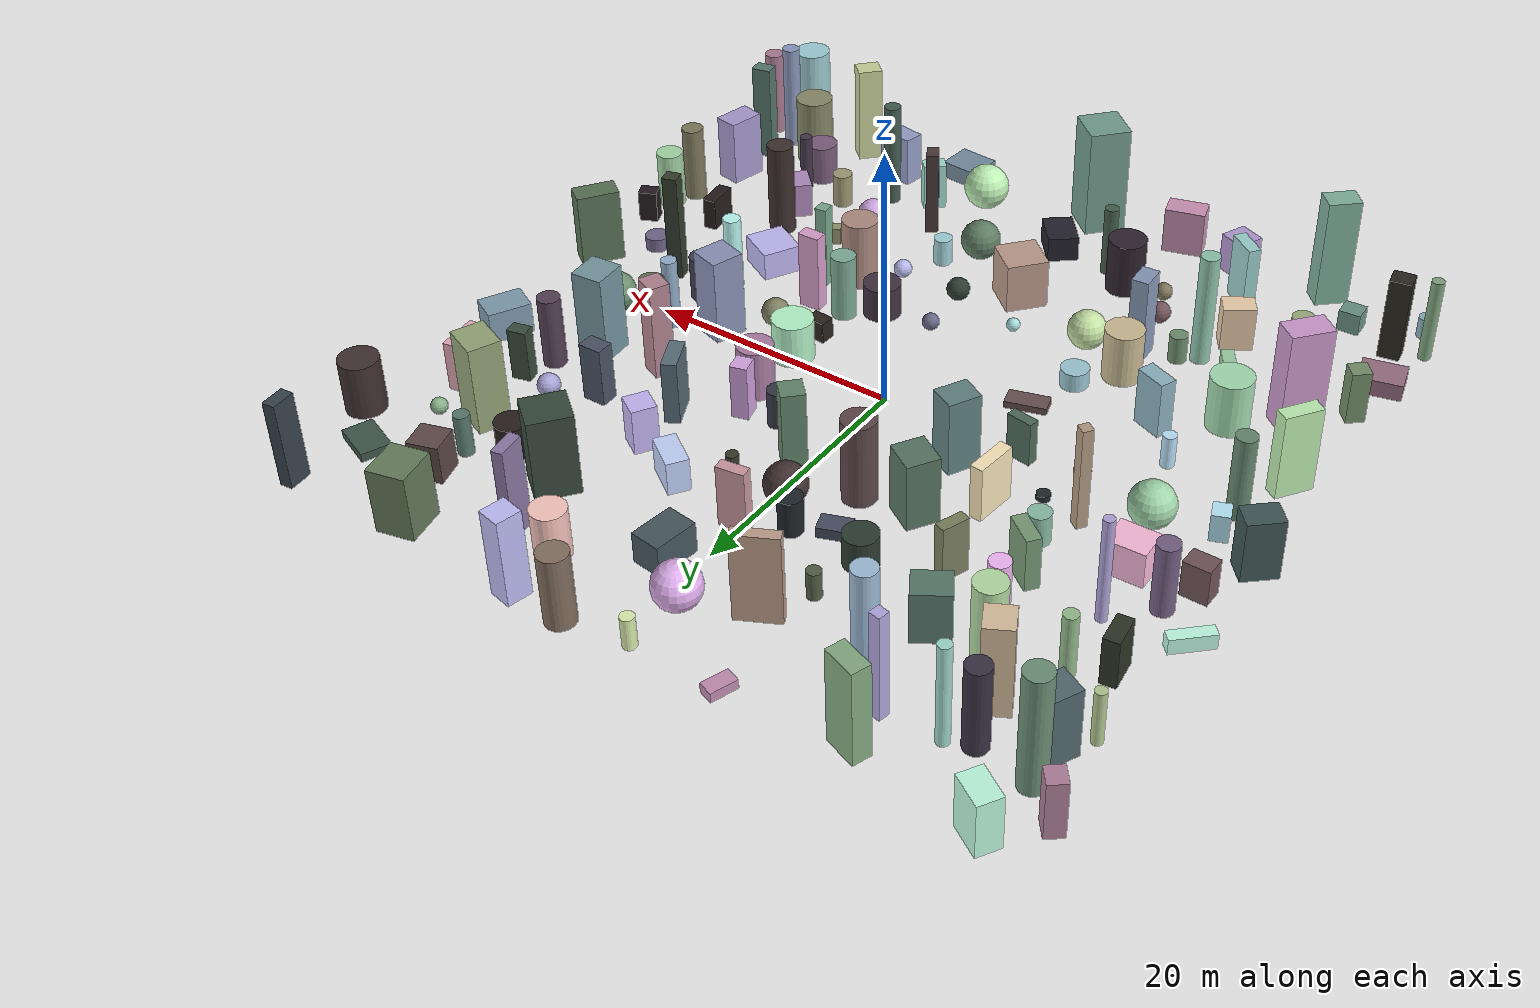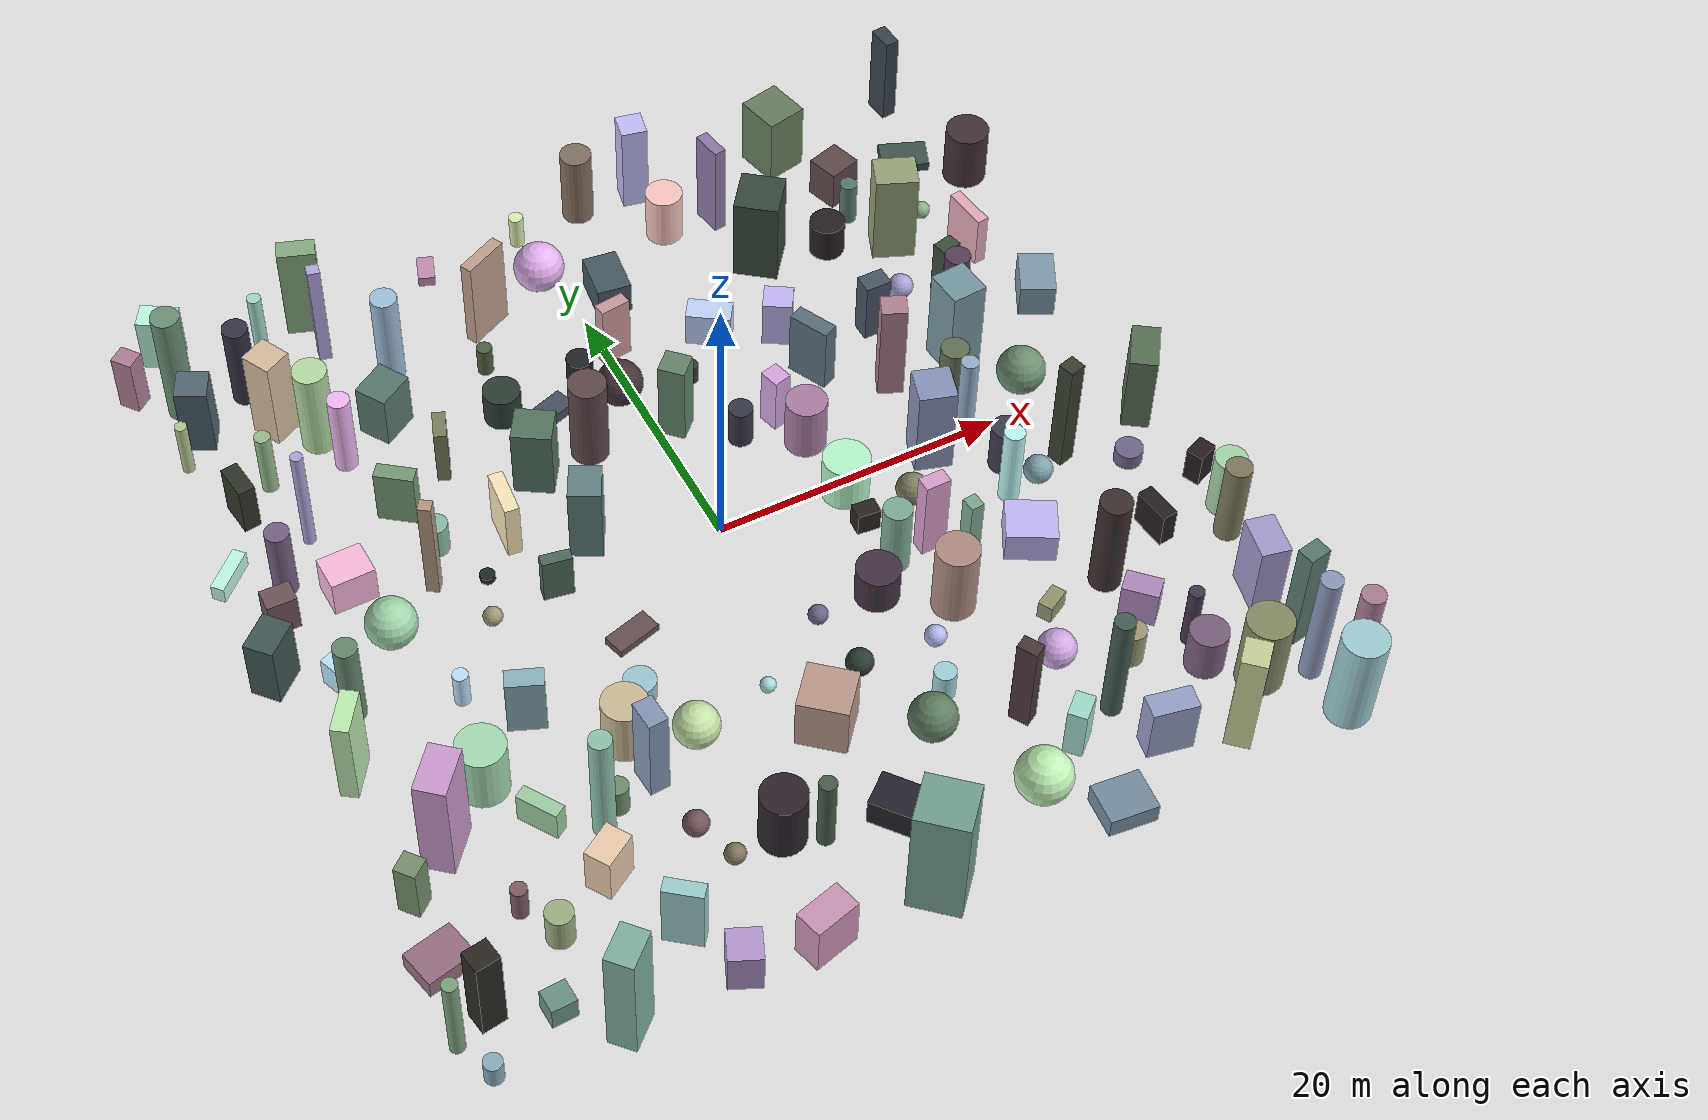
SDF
<?xml version="1.0" ?>
<sdf version="1.9">
  <model name="vio_feature_field">
    <static>true</static>
    <link name="link">
      <collision name="c1">
        <pose>-21.938 20.846 3.484 0 0 2.0470</pose>
        <geometry><box><size>2.138 2.014 6.968</size></box></geometry>
      </collision>
      <visual name="v1">
        <pose>-21.938 20.846 3.484 0 0 2.0470</pose>
        <geometry><box><size>2.138 2.014 6.968</size></box></geometry>
        <material>
          <ambient>0.863 0.760 0.630 1</ambient>
          <diffuse>0.863 0.760 0.630 1</diffuse>
          <specular>0.1 0.1 0.1 1</specular>
        </material>
      </visual>
      <collision name="c2">
        <pose>-28.299 20.146 2.061 0 0 1.3992</pose>
        <geometry><cylinder><radius>0.403</radius><length>4.122</length></cylinder></geometry>
      </collision>
      <visual name="v2">
        <pose>-28.299 20.146 2.061 0 0 1.3992</pose>
        <geometry><cylinder><radius>0.403</radius><length>4.122</length></cylinder></geometry>
        <material>
          <ambient>0.714 0.797 0.581 1</ambient>
          <diffuse>0.714 0.797 0.581 1</diffuse>
          <specular>0.1 0.1 0.1 1</specular>
        </material>
      </visual>
      <collision name="c3">
        <pose>26.716 24.086 0.332 0 0 1.1976</pose>
        <geometry><box><size>2.262 3.336 0.663</size></box></geometry>
      </collision>
      <visual name="v3">
        <pose>26.716 24.086 0.332 0 0 1.1976</pose>
        <geometry><box><size>2.262 3.336 0.663</size></box></geometry>
        <material>
          <ambient>0.247 0.338 0.295 1</ambient>
          <diffuse>0.247 0.338 0.295 1</diffuse>
          <specular>0.1 0.1 0.1 1</specular>
        </material>
      </visual>
      <collision name="c4">
        <pose>-28.258 -16.699 2.083 0 0 0.6873</pose>
        <geometry><box><size>1.429 1.423 4.166</size></box></geometry>
      </collision>
      <visual name="v4">
        <pose>-28.258 -16.699 2.083 0 0 0.6873</pose>
        <geometry><box><size>1.429 1.423 4.166</size></box></geometry>
        <material>
          <ambient>0.466 0.572 0.425 1</ambient>
          <diffuse>0.466 0.572 0.425 1</diffuse>
          <specular>0.1 0.1 0.1 1</specular>
        </material>
      </visual>
      <collision name="c5">
        <pose>21.597 -22.747 1.631 0 0 2.9419</pose>
        <geometry><cylinder><radius>1.253</radius><length>3.261</length></cylinder></geometry>
      </collision>
      <visual name="v5">
        <pose>21.597 -22.747 1.631 0 0 2.9419</pose>
        <geometry><cylinder><radius>1.253</radius><length>3.261</length></cylinder></geometry>
        <material>
          <ambient>0.497 0.375 0.500 1</ambient>
          <diffuse>0.497 0.375 0.500 1</diffuse>
          <specular>0.1 0.1 0.1 1</specular>
        </material>
      </visual>
      <collision name="c6">
        <pose>10.218 -11.798 2.727 0 0 1.5874</pose>
        <geometry><cylinder><radius>1.415</radius><length>5.453</length></cylinder></geometry>
      </collision>
      <visual name="v6">
        <pose>10.218 -11.798 2.727 0 0 1.5874</pose>
        <geometry><cylinder><radius>1.415</radius><length>5.453</length></cylinder></geometry>
        <material>
          <ambient>0.695 0.559 0.519 1</ambient>
          <diffuse>0.695 0.559 0.519 1</diffuse>
          <specular>0.1 0.1 0.1 1</specular>
        </material>
      </visual>
      <collision name="c7">
        <pose>-15.436 17.844 1.982 0 0 2.1190</pose>
        <geometry><box><size>2.282 2.698 3.963</size></box></geometry>
      </collision>
      <visual name="v7">
        <pose>-15.436 17.844 1.982 0 0 2.1190</pose>
        <geometry><box><size>2.282 2.698 3.963</size></box></geometry>
        <material>
          <ambient>0.350 0.479 0.430 1</ambient>
          <diffuse>0.350 0.479 0.430 1</diffuse>
          <specular>0.1 0.1 0.1 1</specular>
        </material>
      </visual>
      <collision name="c8">
        <pose>0.506 16.707 2.440 0 0 0.1366</pose>
        <geometry><box><size>2.122 0.880 4.880</size></box></geometry>
      </collision>
      <visual name="v8">
        <pose>0.506 16.707 2.440 0 0 0.1366</pose>
        <geometry><box><size>2.122 0.880 4.880</size></box></geometry>
        <material>
          <ambient>0.805 0.610 0.633 1</ambient>
          <diffuse>0.805 0.610 0.633 1</diffuse>
          <specular>0.1 0.1 0.1 1</specular>
        </material>
      </visual>
      <collision name="c9">
        <pose>2.377 21.617 1.198 0 0 1.4424</pose>
        <geometry><box><size>3.372 2.360 2.397</size></box></geometry>
      </collision>
      <visual name="v9">
        <pose>2.377 21.617 1.198 0 0 1.4424</pose>
        <geometry><box><size>3.372 2.360 2.397</size></box></geometry>
        <material>
          <ambient>0.278 0.349 0.380 1</ambient>
          <diffuse>0.278 0.349 0.380 1</diffuse>
          <specular>0.1 0.1 0.1 1</specular>
        </material>
      </visual>
      <collision name="c10">
        <pose>27.427 -29.657 3.570 0 0 2.3264</pose>
        <geometry><cylinder><radius>1.463</radius><length>7.139</length></cylinder></geometry>
      </collision>
      <visual name="v10">
        <pose>27.427 -29.657 3.570 0 0 2.3264</pose>
        <geometry><cylinder><radius>1.463</radius><length>7.139</length></cylinder></geometry>
        <material>
          <ambient>0.630 0.822 0.850 1</ambient>
          <diffuse>0.630 0.822 0.850 1</diffuse>
          <specular>0.1 0.1 0.1 1</specular>
        </material>
      </visual>
      <collision name="c11">
        <pose>-26.633 22.201 2.651 0 0 1.1209</pose>
        <geometry><box><size>2.163 2.109 5.302</size></box></geometry>
      </collision>
      <visual name="v11">
        <pose>-26.633 22.201 2.651 0 0 1.1209</pose>
        <geometry><box><size>2.163 2.109 5.302</size></box></geometry>
        <material>
          <ambient>0.328 0.417 0.446 1</ambient>
          <diffuse>0.328 0.417 0.446 1</diffuse>
          <specular>0.1 0.1 0.1 1</specular>
        </material>
      </visual>
      <collision name="c12">
        <pose>7.409 6.747 2.170 0 0 1.8361</pose>
        <geometry><box><size>1.420 1.278 4.340</size></box></geometry>
      </collision>
      <visual name="v12">
        <pose>7.409 6.747 2.170 0 0 1.8361</pose>
        <geometry><box><size>1.420 1.278 4.340</size></box></geometry>
        <material>
          <ambient>0.852 0.667 0.907 1</ambient>
          <diffuse>0.852 0.667 0.907 1</diffuse>
          <specular>0.1 0.1 0.1 1</specular>
        </material>
      </visual>
      <collision name="c13">
        <pose>17.826 18.986 1.298 0 0 0.2615</pose>
        <geometry><cylinder><radius>1.208</radius><length>2.596</length></cylinder></geometry>
      </collision>
      <visual name="v13">
        <pose>17.826 18.986 1.298 0 0 0.2615</pose>
        <geometry><cylinder><radius>1.208</radius><length>2.596</length></cylinder></geometry>
        <material>
          <ambient>0.157 0.123 0.120 1</ambient>
          <diffuse>0.157 0.123 0.120 1</diffuse>
          <specular>0.1 0.1 0.1 1</specular>
        </material>
      </visual>
      <collision name="c14">
        <pose>15.335 -15.026 0.671 0 0 0.5015</pose>
        <geometry><box><size>1.730 0.988 1.342</size></box></geometry>
      </collision>
      <visual name="v14">
        <pose>15.335 -15.026 0.671 0 0 0.5015</pose>
        <geometry><box><size>1.730 0.988 1.342</size></box></geometry>
        <material>
          <ambient>0.590 0.591 0.444 1</ambient>
          <diffuse>0.590 0.591 0.444 1</diffuse>
          <specular>0.1 0.1 0.1 1</specular>
        </material>
      </visual>
      <collision name="c15">
        <pose>-13.625 12.695 2.155 0 0 1.2144</pose>
        <geometry><box><size>2.079 0.864 4.310</size></box></geometry>
      </collision>
      <visual name="v15">
        <pose>-13.625 12.695 2.155 0 0 1.2144</pose>
        <geometry><box><size>2.079 0.864 4.310</size></box></geometry>
        <material>
          <ambient>0.488 0.507 0.375 1</ambient>
          <diffuse>0.488 0.507 0.375 1</diffuse>
          <specular>0.1 0.1 0.1 1</specular>
        </material>
      </visual>
      <collision name="c16">
        <pose>-28.751 -28.928 0.830 0 0 2.2136</pose>
        <geometry><cylinder><radius>0.592</radius><length>1.660</length></cylinder></geometry>
      </collision>
      <visual name="v16">
        <pose>-28.751 -28.928 0.830 0 0 2.2136</pose>
        <geometry><cylinder><radius>0.592</radius><length>1.660</length></cylinder></geometry>
        <material>
          <ambient>0.548 0.691 0.748 1</ambient>
          <diffuse>0.548 0.691 0.748 1</diffuse>
          <specular>0.1 0.1 0.1 1</specular>
        </material>
      </visual>
      <collision name="c17">
        <pose>-16.764 28.536 3.631 0 0 1.2406</pose>
        <geometry><box><size>1.403 2.551 7.261</size></box></geometry>
      </collision>
      <visual name="v17">
        <pose>-16.764 28.536 3.631 0 0 1.2406</pose>
        <geometry><box><size>1.403 2.551 7.261</size></box></geometry>
        <material>
          <ambient>0.535 0.685 0.522 1</ambient>
          <diffuse>0.535 0.685 0.522 1</diffuse>
          <specular>0.1 0.1 0.1 1</specular>
        </material>
      </visual>
      <collision name="c18">
        <pose>7.857 -26.473 1.813 0 0 0.9625</pose>
        <geometry><sphere><radius>1.813</radius></sphere></geometry>
      </collision>
      <visual name="v18">
        <pose>7.857 -26.473 1.813 0 0 0.9625</pose>
        <geometry><sphere><radius>1.813</radius></sphere></geometry>
        <material>
          <ambient>0.753 0.951 0.717 1</ambient>
          <diffuse>0.753 0.951 0.717 1</diffuse>
          <specular>0.1 0.1 0.1 1</specular>
        </material>
      </visual>
      <collision name="c19">
        <pose>26.357 14.631 1.990 0 0 0.1191</pose>
        <geometry><box><size>0.823 3.173 3.979</size></box></geometry>
      </collision>
      <visual name="v19">
        <pose>26.357 14.631 1.990 0 0 0.1191</pose>
        <geometry><box><size>0.823 3.173 3.979</size></box></geometry>
        <material>
          <ambient>0.911 0.679 0.736 1</ambient>
          <diffuse>0.911 0.679 0.736 1</diffuse>
          <specular>0.1 0.1 0.1 1</specular>
        </material>
      </visual>
      <collision name="c20">
        <pose>4.217 -19.709 1.556 0 0 1.5987</pose>
        <geometry><sphere><radius>1.556</radius></sphere></geometry>
      </collision>
      <visual name="v20">
        <pose>4.217 -19.709 1.556 0 0 1.5987</pose>
        <geometry><sphere><radius>1.556</radius></sphere></geometry>
        <material>
          <ambient>0.379 0.498 0.390 1</ambient>
          <diffuse>0.379 0.498 0.390 1</diffuse>
          <specular>0.1 0.1 0.1 1</specular>
        </material>
      </visual>
      <collision name="c21">
        <pose>-17.654 10.449 2.062 0 0 0.9301</pose>
        <geometry><box><size>1.082 2.598 4.123</size></box></geometry>
      </collision>
      <visual name="v21">
        <pose>-17.654 10.449 2.062 0 0 0.9301</pose>
        <geometry><box><size>1.082 2.598 4.123</size></box></geometry>
        <material>
          <ambient>0.477 0.613 0.469 1</ambient>
          <diffuse>0.477 0.613 0.469 1</diffuse>
          <specular>0.1 0.1 0.1 1</specular>
        </material>
      </visual>
      <collision name="c22">
        <pose>16.962 -9.654 1.116 0 0 1.0802</pose>
        <geometry><box><size>3.062 3.317 2.232</size></box></geometry>
      </collision>
      <visual name="v22">
        <pose>16.962 -9.654 1.116 0 0 1.0802</pose>
        <geometry><box><size>3.062 3.317 2.232</size></box></geometry>
        <material>
          <ambient>0.769 0.736 0.973 1</ambient>
          <diffuse>0.769 0.736 0.973 1</diffuse>
          <specular>0.1 0.1 0.1 1</specular>
        </material>
      </visual>
      <collision name="c23">
        <pose>-0.930 29.130 1.209 0 0 0.5331</pose>
        <geometry><cylinder><radius>0.502</radius><length>2.418</length></cylinder></geometry>
      </collision>
      <visual name="v23">
        <pose>-0.930 29.130 1.209 0 0 0.5331</pose>
        <geometry><cylinder><radius>0.502</radius><length>2.418</length></cylinder></geometry>
        <material>
          <ambient>0.884 0.960 0.702 1</ambient>
          <diffuse>0.884 0.960 0.702 1</diffuse>
          <specular>0.1 0.1 0.1 1</specular>
        </material>
      </visual>
      <collision name="c24">
        <pose>15.547 6.013 3.817 0 0 2.7251</pose>
        <geometry><box><size>1.719 1.586 7.634</size></box></geometry>
      </collision>
      <visual name="v24">
        <pose>15.547 6.013 3.817 0 0 2.7251</pose>
        <geometry><box><size>1.719 1.586 7.634</size></box></geometry>
        <material>
          <ambient>0.707 0.525 0.578 1</ambient>
          <diffuse>0.707 0.525 0.578 1</diffuse>
          <specular>0.1 0.1 0.1 1</specular>
        </material>
      </visual>
      <collision name="c25">
        <pose>21.970 17.287 3.500 0 0 1.1876</pose>
        <geometry><box><size>2.461 2.911 7.000</size></box></geometry>
      </collision>
      <visual name="v25">
        <pose>21.970 17.287 3.500 0 0 1.1876</pose>
        <geometry><box><size>2.461 2.911 7.000</size></box></geometry>
        <material>
          <ambient>0.594 0.657 0.479 1</ambient>
          <diffuse>0.594 0.657 0.479 1</diffuse>
          <specular>0.1 0.1 0.1 1</specular>
        </material>
      </visual>
      <collision name="c26">
        <pose>-25.095 -13.997 4.030 0 0 0.8708</pose>
        <geometry><box><size>3.298 2.036 8.061</size></box></geometry>
      </collision>
      <visual name="v26">
        <pose>-25.095 -13.997 4.030 0 0 0.8708</pose>
        <geometry><box><size>3.298 2.036 8.061</size></box></geometry>
        <material>
          <ambient>0.813 0.615 0.821 1</ambient>
          <diffuse>0.813 0.615 0.821 1</diffuse>
          <specular>0.1 0.1 0.1 1</specular>
        </material>
      </visual>
      <collision name="c27">
        <pose>-29.257 10.225 0.594 0 0 0.7528</pose>
        <geometry><box><size>3.190 0.908 1.188</size></box></geometry>
      </collision>
      <visual name="v27">
        <pose>-29.257 10.225 0.594 0 0 0.7528</pose>
        <geometry><box><size>3.190 0.908 1.188</size></box></geometry>
        <material>
          <ambient>0.766 1.000 0.915 1</ambient>
          <diffuse>0.766 1.000 0.915 1</diffuse>
          <specular>0.1 0.1 0.1 1</specular>
        </material>
      </visual>
      <collision name="c28">
        <pose>-23.067 -19.957 1.238 0 0 2.8613</pose>
        <geometry><cylinder><radius>0.523</radius><length>2.476</length></cylinder></geometry>
      </collision>
      <visual name="v28">
        <pose>-23.067 -19.957 1.238 0 0 2.8613</pose>
        <geometry><cylinder><radius>0.523</radius><length>2.476</length></cylinder></geometry>
        <material>
          <ambient>0.497 0.373 0.398 1</ambient>
          <diffuse>0.497 0.373 0.398 1</diffuse>
          <specular>0.1 0.1 0.1 1</specular>
        </material>
      </visual>
      <collision name="c29">
        <pose>24.553 -12.359 1.290 0 0 0.1245</pose>
        <geometry><box><size>1.070 2.561 2.579</size></box></geometry>
      </collision>
      <visual name="v29">
        <pose>24.553 -12.359 1.290 0 0 0.1245</pose>
        <geometry><box><size>1.070 2.561 2.579</size></box></geometry>
        <material>
          <ambient>0.151 0.115 0.119 1</ambient>
          <diffuse>0.151 0.115 0.119 1</diffuse>
          <specular>0.1 0.1 0.1 1</specular>
        </material>
      </visual>
      <collision name="c30">
        <pose>-12.267 5.794 2.134 0 0 3.0468</pose>
        <geometry><box><size>0.970 3.266 4.269</size></box></geometry>
      </collision>
      <visual name="v30">
        <pose>-12.267 5.794 2.134 0 0 3.0468</pose>
        <geometry><box><size>0.970 3.266 4.269</size></box></geometry>
        <material>
          <ambient>1.000 0.924 0.744 1</ambient>
          <diffuse>1.000 0.924 0.744 1</diffuse>
          <specular>0.1 0.1 0.1 1</specular>
        </material>
      </visual>
      <collision name="c31">
        <pose>29.003 -3.126 3.004 0 0 0.9638</pose>
        <geometry><box><size>3.340 1.854 6.007</size></box></geometry>
      </collision>
      <visual name="v31">
        <pose>29.003 -3.126 3.004 0 0 0.9638</pose>
        <geometry><box><size>3.340 1.854 6.007</size></box></geometry>
        <material>
          <ambient>0.354 0.450 0.341 1</ambient>
          <diffuse>0.354 0.450 0.341 1</diffuse>
          <specular>0.1 0.1 0.1 1</specular>
        </material>
      </visual>
      <collision name="c32">
        <pose>20.828 23.610 1.502 0 0 1.8723</pose>
        <geometry><box><size>2.269 2.363 3.004</size></box></geometry>
      </collision>
      <visual name="v32">
        <pose>20.828 23.610 1.502 0 0 1.8723</pose>
        <geometry><box><size>2.269 2.363 3.004</size></box></geometry>
        <material>
          <ambient>0.373 0.294 0.282 1</ambient>
          <diffuse>0.373 0.294 0.282 1</diffuse>
          <specular>0.1 0.1 0.1 1</specular>
        </material>
      </visual>
      <collision name="c33">
        <pose>-15.374 -25.660 2.570 0 0 0.9136</pose>
        <geometry><box><size>1.003 2.516 5.140</size></box></geometry>
      </collision>
      <visual name="v33">
        <pose>-15.374 -25.660 2.570 0 0 0.9136</pose>
        <geometry><box><size>1.003 2.516 5.140</size></box></geometry>
        <material>
          <ambient>0.618 0.826 0.817 1</ambient>
          <diffuse>0.618 0.826 0.817 1</diffuse>
          <specular>0.1 0.1 0.1 1</specular>
        </material>
      </visual>
      <collision name="c34">
        <pose>21.759 -20.749 2.356 0 0 2.9821</pose>
        <geometry><cylinder><radius>0.493</radius><length>4.712</length></cylinder></geometry>
      </collision>
      <visual name="v34">
        <pose>21.759 -20.749 2.356 0 0 2.9821</pose>
        <geometry><cylinder><radius>0.493</radius><length>4.712</length></cylinder></geometry>
        <material>
          <ambient>0.266 0.215 0.295 1</ambient>
          <diffuse>0.266 0.215 0.295 1</diffuse>
          <specular>0.1 0.1 0.1 1</specular>
        </material>
      </visual>
      <collision name="c35">
        <pose>-12.391 23.626 0.548 0 0 0.9930</pose>
        <geometry><sphere><radius>0.548</radius></sphere></geometry>
      </collision>
      <visual name="v35">
        <pose>-12.391 23.626 0.548 0 0 0.9930</pose>
        <geometry><sphere><radius>0.548</radius></sphere></geometry>
        <material>
          <ambient>0.893 0.693 0.941 1</ambient>
          <diffuse>0.893 0.693 0.941 1</diffuse>
          <specular>0.1 0.1 0.1 1</specular>
        </material>
      </visual>
      <collision name="c36">
        <pose>18.495 2.956 2.528 0 0 1.2432</pose>
        <geometry><cylinder><radius>0.944</radius><length>5.056</length></cylinder></geometry>
      </collision>
      <visual name="v36">
        <pose>18.495 2.956 2.528 0 0 1.2432</pose>
        <geometry><cylinder><radius>0.944</radius><length>5.056</length></cylinder></geometry>
        <material>
          <ambient>0.387 0.454 0.332 1</ambient>
          <diffuse>0.387 0.454 0.332 1</diffuse>
          <specular>0.1 0.1 0.1 1</specular>
        </material>
      </visual>
      <collision name="c37">
        <pose>-21.703 -22.492 1.314 0 0 1.2600</pose>
        <geometry><cylinder><radius>0.877</radius><length>2.628</length></cylinder></geometry>
      </collision>
      <visual name="v37">
        <pose>-21.703 -22.492 1.314 0 0 1.2600</pose>
        <geometry><cylinder><radius>0.877</radius><length>2.628</length></cylinder></geometry>
        <material>
          <ambient>0.621 0.699 0.510 1</ambient>
          <diffuse>0.621 0.699 0.510 1</diffuse>
          <specular>0.1 0.1 0.1 1</specular>
        </material>
      </visual>
      <collision name="c38">
        <pose>-29.551 1.722 2.354 0 0 2.2978</pose>
        <geometry><box><size>1.983 2.654 4.708</size></box></geometry>
      </collision>
      <visual name="v38">
        <pose>-29.551 1.722 2.354 0 0 2.2978</pose>
        <geometry><box><size>1.983 2.654 4.708</size></box></geometry>
        <material>
          <ambient>0.255 0.340 0.337 1</ambient>
          <diffuse>0.255 0.340 0.337 1</diffuse>
          <specular>0.1 0.1 0.1 1</specular>
        </material>
      </visual>
      <collision name="c39">
        <pose>-1.270 -16.496 1.973 0 0 0.8646</pose>
        <geometry><box><size>3.249 3.278 3.945</size></box></geometry>
      </collision>
      <visual name="v39">
        <pose>-1.270 -16.496 1.973 0 0 0.8646</pose>
        <geometry><box><size>3.249 3.278 3.945</size></box></geometry>
        <material>
          <ambient>0.747 0.612 0.553 1</ambient>
          <diffuse>0.747 0.612 0.553 1</diffuse>
          <specular>0.1 0.1 0.1 1</specular>
        </material>
      </visual>
      <collision name="c40">
        <pose>-19.423 -14.964 1.136 0 0 2.1414</pose>
        <geometry><box><size>2.846 0.941 2.272</size></box></geometry>
      </collision>
      <visual name="v40">
        <pose>-19.423 -14.964 1.136 0 0 2.1414</pose>
        <geometry><box><size>2.846 0.941 2.272</size></box></geometry>
        <material>
          <ambient>0.622 0.818 0.641 1</ambient>
          <diffuse>0.622 0.818 0.641 1</diffuse>
          <specular>0.1 0.1 0.1 1</specular>
        </material>
      </visual>
      <collision name="c41">
        <pose>7.707 -13.948 0.709 0 0 2.4371</pose>
        <geometry><sphere><radius>0.709</radius></sphere></geometry>
      </collision>
      <visual name="v41">
        <pose>7.707 -13.948 0.709 0 0 2.4371</pose>
        <geometry><sphere><radius>0.709</radius></sphere></geometry>
        <material>
          <ambient>0.717 0.728 0.936 1</ambient>
          <diffuse>0.717 0.728 0.936 1</diffuse>
          <specular>0.1 0.1 0.1 1</specular>
        </material>
      </visual>
      <collision name="c42">
        <pose>12.024 -3.296 1.074 0 0 2.5218</pose>
        <geometry><sphere><radius>1.074</radius></sphere></geometry>
      </collision>
      <visual name="v42">
        <pose>12.024 -3.296 1.074 0 0 2.5218</pose>
        <geometry><sphere><radius>1.074</radius></sphere></geometry>
        <material>
          <ambient>0.509 0.507 0.382 1</ambient>
          <diffuse>0.509 0.507 0.382 1</diffuse>
          <specular>0.1 0.1 0.1 1</specular>
        </material>
      </visual>
      <collision name="c43">
        <pose>-10.472 -22.420 0.679 0 0 1.8871</pose>
        <geometry><sphere><radius>0.679</radius></sphere></geometry>
      </collision>
      <visual name="v43">
        <pose>-10.472 -22.420 0.679 0 0 1.8871</pose>
        <geometry><sphere><radius>0.679</radius></sphere></geometry>
        <material>
          <ambient>0.506 0.464 0.370 1</ambient>
          <diffuse>0.506 0.464 0.370 1</diffuse>
          <specular>0.1 0.1 0.1 1</specular>
        </material>
      </visual>
      <collision name="c44">
        <pose>-12.271 -15.107 3.423 0 0 0.0661</pose>
        <geometry><box><size>1.313 1.985 6.846</size></box></geometry>
      </collision>
      <visual name="v44">
        <pose>-12.271 -15.107 3.423 0 0 0.0661</pose>
        <geometry><box><size>1.313 1.985 6.846</size></box></geometry>
        <material>
          <ambient>0.534 0.606 0.726 1</ambient>
          <diffuse>0.534 0.606 0.726 1</diffuse>
          <specular>0.1 0.1 0.1 1</specular>
        </material>
      </visual>
      <collision name="c45">
        <pose>20.120 -17.604 1.425 0 0 0.7882</pose>
        <geometry><box><size>1.538 2.381 2.849</size></box></geometry>
      </collision>
      <visual name="v45">
        <pose>20.120 -17.604 1.425 0 0 0.7882</pose>
        <geometry><box><size>1.538 2.381 2.849</size></box></geometry>
        <material>
          <ambient>0.697 0.551 0.752 1</ambient>
          <diffuse>0.697 0.551 0.752 1</diffuse>
          <specular>0.1 0.1 0.1 1</specular>
        </material>
      </visual>
      <collision name="c46">
        <pose>18.519 28.417 2.545 0 0 1.7924</pose>
        <geometry><box><size>3.110 2.876 5.090</size></box></geometry>
      </collision>
      <visual name="v46">
        <pose>18.519 28.417 2.545 0 0 1.7924</pose>
        <geometry><box><size>3.110 2.876 5.090</size></box></geometry>
        <material>
          <ambient>0.410 0.500 0.370 1</ambient>
          <diffuse>0.410 0.500 0.370 1</diffuse>
          <specular>0.1 0.1 0.1 1</specular>
        </material>
      </visual>
      <collision name="c47">
        <pose>-11.325 0.182 1.734 0 0 1.4123</pose>
        <geometry><box><size>0.802 1.994 3.469</size></box></geometry>
      </collision>
      <visual name="v47">
        <pose>-11.325 0.182 1.734 0 0 1.4123</pose>
        <geometry><box><size>0.802 1.994 3.469</size></box></geometry>
        <material>
          <ambient>0.311 0.424 0.357 1</ambient>
          <diffuse>0.311 0.424 0.357 1</diffuse>
          <specular>0.1 0.1 0.1 1</specular>
        </material>
      </visual>
      <collision name="c48">
        <pose>16.985 11.005 2.317 0 0 0.0122</pose>
        <geometry><box><size>1.819 1.351 4.634</size></box></geometry>
      </collision>
      <visual name="v48">
        <pose>16.985 11.005 2.317 0 0 0.0122</pose>
        <geometry><box><size>1.819 1.351 4.634</size></box></geometry>
        <material>
          <ambient>0.292 0.336 0.398 1</ambient>
          <diffuse>0.292 0.336 0.398 1</diffuse>
          <specular>0.1 0.1 0.1 1</specular>
        </material>
      </visual>
      <collision name="c49">
        <pose>20.076 -5.462 0.958 0 0 0.5351</pose>
        <geometry><sphere><radius>0.958</radius></sphere></geometry>
      </collision>
      <visual name="v49">
        <pose>20.076 -5.462 0.958 0 0 0.5351</pose>
        <geometry><sphere><radius>0.958</radius></sphere></geometry>
        <material>
          <ambient>0.507 0.652 0.689 1</ambient>
          <diffuse>0.507 0.652 0.689 1</diffuse>
          <specular>0.1 0.1 0.1 1</specular>
        </material>
      </visual>
      <collision name="c50">
        <pose>-8.435 -29.789 1.873 0 0 1.8360</pose>
        <geometry><box><size>1.894 3.125 3.747</size></box></geometry>
      </collision>
      <visual name="v50">
        <pose>-8.435 -29.789 1.873 0 0 1.8360</pose>
        <geometry><box><size>1.894 3.125 3.747</size></box></geometry>
        <material>
          <ambient>0.809 0.590 0.722 1</ambient>
          <diffuse>0.809 0.590 0.722 1</diffuse>
          <specular>0.1 0.1 0.1 1</specular>
        </material>
      </visual>
      <collision name="c51">
        <pose>14.926 -0.438 3.407 0 0 1.2786</pose>
        <geometry><box><size>2.552 2.500 6.814</size></box></geometry>
      </collision>
      <visual name="v51">
        <pose>14.926 -0.438 3.407 0 0 1.2786</pose>
        <geometry><box><size>2.552 2.500 6.814</size></box></geometry>
        <material>
          <ambient>0.549 0.588 0.733 1</ambient>
          <diffuse>0.549 0.588 0.733 1</diffuse>
          <specular>0.1 0.1 0.1 1</specular>
        </material>
      </visual>
      <collision name="c52">
        <pose>6.328 -9.033 1.338 0 0 1.7098</pose>
        <geometry><cylinder><radius>1.449</radius><length>2.675</length></cylinder></geometry>
      </collision>
      <visual name="v52">
        <pose>6.328 -9.033 1.338 0 0 1.7098</pose>
        <geometry><cylinder><radius>1.449</radius><length>2.675</length></cylinder></geometry>
        <material>
          <ambient>0.263 0.198 0.264 1</ambient>
          <diffuse>0.263 0.198 0.264 1</diffuse>
          <specular>0.1 0.1 0.1 1</specular>
        </material>
      </visual>
      <collision name="c53">
        <pose>6.300 -17.467 1.093 0 0 0.2353</pose>
        <geometry><cylinder><radius>0.723</radius><length>2.186</length></cylinder></geometry>
      </collision>
      <visual name="v53">
        <pose>6.300 -17.467 1.093 0 0 0.2353</pose>
        <geometry><cylinder><radius>0.723</radius><length>2.186</length></cylinder></geometry>
        <material>
          <ambient>0.645 0.837 0.872 1</ambient>
          <diffuse>0.645 0.837 0.872 1</diffuse>
          <specular>0.1 0.1 0.1 1</specular>
        </material>
      </visual>
      <collision name="c54">
        <pose>20.628 -28.168 4.067 0 0 2.3926</pose>
        <geometry><box><size>1.655 1.966 8.135</size></box></geometry>
      </collision>
      <visual name="v54">
        <pose>20.628 -28.168 4.067 0 0 2.3926</pose>
        <geometry><box><size>1.655 1.966 8.135</size></box></geometry>
        <material>
          <ambient>0.798 0.832 0.615 1</ambient>
          <diffuse>0.798 0.832 0.615 1</diffuse>
          <specular>0.1 0.1 0.1 1</specular>
        </material>
      </visual>
      <collision name="c55">
        <pose>-8.335 15.083 1.234 0 0 0.9597</pose>
        <geometry><cylinder><radius>1.262</radius><length>2.468</length></cylinder></geometry>
      </collision>
      <visual name="v55">
        <pose>-8.335 15.083 1.234 0 0 0.9597</pose>
        <geometry><cylinder><radius>1.262</radius><length>2.468</length></cylinder></geometry>
        <material>
          <ambient>0.176 0.239 0.201 1</ambient>
          <diffuse>0.176 0.239 0.201 1</diffuse>
          <specular>0.1 0.1 0.1 1</specular>
        </material>
      </visual>
      <collision name="c56">
        <pose>-0.458 -24.002 1.003 0 0 0.6803</pose>
        <geometry><box><size>2.413 3.200 2.006</size></box></geometry>
      </collision>
      <visual name="v56">
        <pose>-0.458 -24.002 1.003 0 0 0.6803</pose>
        <geometry><box><size>2.413 3.200 2.006</size></box></geometry>
        <material>
          <ambient>0.140 0.129 0.174 1</ambient>
          <diffuse>0.140 0.129 0.174 1</diffuse>
          <specular>0.1 0.1 0.1 1</specular>
        </material>
      </visual>
      <collision name="c57">
        <pose>11.558 -24.286 1.919 0 0 0.7280</pose>
        <geometry><box><size>1.820 1.255 3.837</size></box></geometry>
      </collision>
      <visual name="v57">
        <pose>11.558 -24.286 1.919 0 0 0.7280</pose>
        <geometry><box><size>1.820 1.255 3.837</size></box></geometry>
        <material>
          <ambient>0.640 0.872 0.816 1</ambient>
          <diffuse>0.640 0.872 0.816 1</diffuse>
          <specular>0.1 0.1 0.1 1</specular>
        </material>
      </visual>
      <collision name="c58">
        <pose>29.664 -27.227 3.629 0 0 1.2037</pose>
        <geometry><cylinder><radius>0.783</radius><length>7.258</length></cylinder></geometry>
      </collision>
      <visual name="v58">
        <pose>29.664 -27.227 3.629 0 0 1.2037</pose>
        <geometry><cylinder><radius>0.783</radius><length>7.258</length></cylinder></geometry>
        <material>
          <ambient>0.676 0.494 0.583 1</ambient>
          <diffuse>0.676 0.494 0.583 1</diffuse>
          <specular>0.1 0.1 0.1 1</specular>
        </material>
      </visual>
      <collision name="c59">
        <pose>-6.004 22.802 3.462 0 0 0.4561</pose>
        <geometry><box><size>3.267 0.841 6.924</size></box></geometry>
      </collision>
      <visual name="v59">
        <pose>-6.004 22.802 3.462 0 0 0.4561</pose>
        <geometry><box><size>3.267 0.841 6.924</size></box></geometry>
        <material>
          <ambient>0.762 0.633 0.561 1</ambient>
          <diffuse>0.762 0.633 0.561 1</diffuse>
          <specular>0.1 0.1 0.1 1</specular>
        </material>
      </visual>
      <collision name="c60">
        <pose>-7.231 -22.201 2.190 0 0 0.1114</pose>
        <geometry><cylinder><radius>1.487</radius><length>4.381</length></cylinder></geometry>
      </collision>
      <visual name="v60">
        <pose>-7.231 -22.201 2.190 0 0 0.1114</pose>
        <geometry><cylinder><radius>1.487</radius><length>4.381</length></cylinder></geometry>
        <material>
          <ambient>0.185 0.138 0.183 1</ambient>
          <diffuse>0.185 0.138 0.183 1</diffuse>
          <specular>0.1 0.1 0.1 1</specular>
        </material>
      </visual>
      <collision name="c61">
        <pose>28.176 8.496 1.245 0 0 1.0983</pose>
        <geometry><box><size>3.325 2.394 2.491</size></box></geometry>
      </collision>
      <visual name="v61">
        <pose>28.176 8.496 1.245 0 0 1.0983</pose>
        <geometry><box><size>3.325 2.394 2.491</size></box></geometry>
        <material>
          <ambient>0.503 0.620 0.690 1</ambient>
          <diffuse>0.503 0.620 0.690 1</diffuse>
          <specular>0.1 0.1 0.1 1</specular>
        </material>
      </visual>
      <collision name="c62">
        <pose>-4.553 9.743 3.268 0 0 2.3631</pose>
        <geometry><cylinder><radius>1.265</radius><length>6.536</length></cylinder></geometry>
      </collision>
      <visual name="v62">
        <pose>-4.553 9.743 3.268 0 0 2.3631</pose>
        <geometry><cylinder><radius>1.265</radius><length>6.536</length></cylinder></geometry>
        <material>
          <ambient>0.378 0.285 0.300 1</ambient>
          <diffuse>0.378 0.285 0.300 1</diffuse>
          <specular>0.1 0.1 0.1 1</specular>
        </material>
      </visual>
      <collision name="c63">
        <pose>-20.939 25.119 3.875 0 0 0.2866</pose>
        <geometry><cylinder><radius>0.463</radius><length>7.749</length></cylinder></geometry>
      </collision>
      <visual name="v63">
        <pose>-20.939 25.119 3.875 0 0 0.2866</pose>
        <geometry><cylinder><radius>0.463</radius><length>7.749</length></cylinder></geometry>
        <material>
          <ambient>0.634 0.862 0.815 1</ambient>
          <diffuse>0.634 0.862 0.815 1</diffuse>
          <specular>0.1 0.1 0.1 1</specular>
        </material>
      </visual>
      <collision name="c64">
        <pose>-7.785 29.081 0.373 0 0 1.2415</pose>
        <geometry><box><size>1.997 1.146 0.745</size></box></geometry>
      </collision>
      <visual name="v64">
        <pose>-7.785 29.081 0.373 0 0 1.2415</pose>
        <geometry><box><size>1.997 1.146 0.745</size></box></geometry>
        <material>
          <ambient>0.777 0.568 0.713 1</ambient>
          <diffuse>0.777 0.568 0.713 1</diffuse>
          <specular>0.1 0.1 0.1 1</specular>
        </material>
      </visual>
      <collision name="c65">
        <pose>-27.948 -6.946 3.350 0 0 2.5350</pose>
        <geometry><box><size>1.151 2.945 6.700</size></box></geometry>
      </collision>
      <visual name="v65">
        <pose>-27.948 -6.946 3.350 0 0 2.5350</pose>
        <geometry><box><size>1.151 2.945 6.700</size></box></geometry>
        <material>
          <ambient>0.757 0.947 0.710 1</ambient>
          <diffuse>0.757 0.947 0.710 1</diffuse>
          <specular>0.1 0.1 0.1 1</specular>
        </material>
      </visual>
      <collision name="c66">
        <pose>13.163 20.087 3.216 0 0 0.9152</pose>
        <geometry><box><size>3.221 3.045 6.431</size></box></geometry>
      </collision>
      <visual name="v66">
        <pose>13.163 20.087 3.216 0 0 0.9152</pose>
        <geometry><box><size>3.221 3.045 6.431</size></box></geometry>
        <material>
          <ambient>0.215 0.289 0.233 1</ambient>
          <diffuse>0.215 0.289 0.233 1</diffuse>
          <specular>0.1 0.1 0.1 1</specular>
        </material>
      </visual>
      <collision name="c67">
        <pose>-1.218 24.773 1.723 0 0 2.9074</pose>
        <geometry><sphere><radius>1.723</radius></sphere></geometry>
      </collision>
      <visual name="v67">
        <pose>-1.218 24.773 1.723 0 0 2.9074</pose>
        <geometry><sphere><radius>1.723</radius></sphere></geometry>
        <material>
          <ambient>0.907 0.707 0.960 1</ambient>
          <diffuse>0.907 0.707 0.960 1</diffuse>
          <specular>0.1 0.1 0.1 1</specular>
        </material>
      </visual>
      <collision name="c68">
        <pose>-21.925 1.423 1.676 0 0 2.2083</pose>
        <geometry><sphere><radius>1.676</radius></sphere></geometry>
      </collision>
      <visual name="v68">
        <pose>-21.925 1.423 1.676 0 0 2.2083</pose>
        <geometry><sphere><radius>1.676</radius></sphere></geometry>
        <material>
          <ambient>0.634 0.844 0.673 1</ambient>
          <diffuse>0.634 0.844 0.673 1</diffuse>
          <specular>0.1 0.1 0.1 1</specular>
        </material>
      </visual>
      <collision name="c69">
        <pose>-5.333 13.678 0.415 0 0 0.3360</pose>
        <geometry><box><size>2.273 1.517 0.831</size></box></geometry>
      </collision>
      <visual name="v69">
        <pose>-5.333 13.678 0.415 0 0 0.3360</pose>
        <geometry><box><size>2.273 1.517 0.831</size></box></geometry>
        <material>
          <ambient>0.289 0.311 0.387 1</ambient>
          <diffuse>0.289 0.311 0.387 1</diffuse>
          <specular>0.1 0.1 0.1 1</specular>
        </material>
      </visual>
      <collision name="c70">
        <pose>11.480 -29.670 0.716 0 0 3.0498</pose>
        <geometry><box><size>3.195 2.817 1.432</size></box></geometry>
      </collision>
      <visual name="v70">
        <pose>11.480 -29.670 0.716 0 0 3.0498</pose>
        <geometry><box><size>3.195 2.817 1.432</size></box></geometry>
        <material>
          <ambient>0.465 0.562 0.637 1</ambient>
          <diffuse>0.465 0.562 0.637 1</diffuse>
          <specular>0.1 0.1 0.1 1</specular>
        </material>
      </visual>
      <collision name="c71">
        <pose>8.200 29.672 3.365 0 0 2.9422</pose>
        <geometry><box><size>1.795 1.886 6.731</size></box></geometry>
      </collision>
      <visual name="v71">
        <pose>8.200 29.672 3.365 0 0 2.9422</pose>
        <geometry><box><size>1.795 1.886 6.731</size></box></geometry>
        <material>
          <ambient>0.763 0.758 0.987 1</ambient>
          <diffuse>0.763 0.758 0.987 1</diffuse>
          <specular>0.1 0.1 0.1 1</specular>
        </material>
      </visual>
      <collision name="c72">
        <pose>-8.730 -5.088 0.278 0 0 1.8522</pose>
        <geometry><box><size>1.503 3.116 0.556</size></box></geometry>
      </collision>
      <visual name="v72">
        <pose>-8.730 -5.088 0.278 0 0 1.8522</pose>
        <geometry><box><size>1.503 3.116 0.556</size></box></geometry>
        <material>
          <ambient>0.413 0.317 0.319 1</ambient>
          <diffuse>0.413 0.317 0.319 1</diffuse>
          <specular>0.1 0.1 0.1 1</specular>
        </material>
      </visual>
      <collision name="c73">
        <pose>-0.852 12.928 1.574 0 0 0.2871</pose>
        <geometry><sphere><radius>1.574</radius></sphere></geometry>
      </collision>
      <visual name="v73">
        <pose>-0.852 12.928 1.574 0 0 0.2871</pose>
        <geometry><sphere><radius>1.574</radius></sphere></geometry>
        <material>
          <ambient>0.263 0.197 0.211 1</ambient>
          <diffuse>0.263 0.197 0.211 1</diffuse>
          <specular>0.1 0.1 0.1 1</specular>
        </material>
      </visual>
      <collision name="c74">
        <pose>2.069 -9.198 0.655 0 0 1.7368</pose>
        <geometry><sphere><radius>0.655</radius></sphere></geometry>
      </collision>
      <visual name="v74">
        <pose>2.069 -9.198 0.655 0 0 1.7368</pose>
        <geometry><sphere><radius>0.655</radius></sphere></geometry>
        <material>
          <ambient>0.417 0.412 0.538 1</ambient>
          <diffuse>0.417 0.412 0.538 1</diffuse>
          <specular>0.1 0.1 0.1 1</specular>
        </material>
      </visual>
      <collision name="c75">
        <pose>29.524 -12.684 2.318 0 0 0.6743</pose>
        <geometry><cylinder><radius>1.054</radius><length>4.635</length></cylinder></geometry>
      </collision>
      <visual name="v75">
        <pose>29.524 -12.684 2.318 0 0 0.6743</pose>
        <geometry><cylinder><radius>1.054</radius><length>4.635</length></cylinder></geometry>
        <material>
          <ambient>0.660 0.859 0.665 1</ambient>
          <diffuse>0.660 0.859 0.665 1</diffuse>
          <specular>0.1 0.1 0.1 1</specular>
        </material>
      </visual>
      <collision name="c76">
        <pose>-0.842 -29.486 4.453 0 0 0.8405</pose>
        <geometry><box><size>3.300 3.415 8.905</size></box></geometry>
      </collision>
      <visual name="v76">
        <pose>-0.842 -29.486 4.453 0 0 0.8405</pose>
        <geometry><box><size>3.300 3.415 8.905</size></box></geometry>
        <material>
          <ambient>0.460 0.630 0.567 1</ambient>
          <diffuse>0.460 0.630 0.567 1</diffuse>
          <specular>0.1 0.1 0.1 1</specular>
        </material>
      </visual>
      <collision name="c77">
        <pose>-17.136 -7.939 2.223 0 0 2.7643</pose>
        <geometry><box><size>2.435 1.289 4.447</size></box></geometry>
      </collision>
      <visual name="v77">
        <pose>-17.136 -7.939 2.223 0 0 2.7643</pose>
        <geometry><box><size>2.435 1.289 4.447</size></box></geometry>
        <material>
          <ambient>0.557 0.712 0.757 1</ambient>
          <diffuse>0.557 0.712 0.757 1</diffuse>
          <specular>0.1 0.1 0.1 1</specular>
        </material>
      </visual>
      <collision name="c78">
        <pose>-18.036 4.054 4.002 0 0 0.9591</pose>
        <geometry><box><size>0.811 0.854 8.005</size></box></geometry>
      </collision>
      <visual name="v78">
        <pose>-18.036 4.054 4.002 0 0 0.9591</pose>
        <geometry><box><size>0.811 0.854 8.005</size></box></geometry>
        <material>
          <ambient>0.707 0.613 0.516 1</ambient>
          <diffuse>0.707 0.613 0.516 1</diffuse>
          <specular>0.1 0.1 0.1 1</specular>
        </material>
      </visual>
      <collision name="c79">
        <pose>-27.539 -25.357 3.317 0 0 0.1563</pose>
        <geometry><box><size>1.656 1.527 6.634</size></box></geometry>
      </collision>
      <visual name="v79">
        <pose>-27.539 -25.357 3.317 0 0 0.1563</pose>
        <geometry><box><size>1.656 1.527 6.634</size></box></geometry>
        <material>
          <ambient>0.162 0.154 0.119 1</ambient>
          <diffuse>0.162 0.154 0.119 1</diffuse>
          <specular>0.1 0.1 0.1 1</specular>
        </material>
      </visual>
      <collision name="c80">
        <pose>20.600 6.370 3.500 0 0 1.6579</pose>
        <geometry><box><size>2.633 2.476 7.000</size></box></geometry>
      </collision>
      <visual name="v80">
        <pose>20.600 6.370 3.500 0 0 1.6579</pose>
        <geometry><box><size>2.633 2.476 7.000</size></box></geometry>
        <material>
          <ambient>0.471 0.602 0.642 1</ambient>
          <diffuse>0.471 0.602 0.642 1</diffuse>
          <specular>0.1 0.1 0.1 1</specular>
        </material>
      </visual>
      <collision name="c81">
        <pose>20.495 20.894 1.642 0 0 2.6676</pose>
        <geometry><cylinder><radius>0.592</radius><length>3.285</length></cylinder></geometry>
      </collision>
      <visual name="v81">
        <pose>20.495 20.894 1.642 0 0 2.6676</pose>
        <geometry><cylinder><radius>0.592</radius><length>3.285</length></cylinder></geometry>
        <material>
          <ambient>0.354 0.485 0.436 1</ambient>
          <diffuse>0.354 0.485 0.436 1</diffuse>
          <specular>0.1 0.1 0.1 1</specular>
        </material>
      </visual>
      <collision name="c82">
        <pose>-22.928 6.060 1.360 0 0 0.0257</pose>
        <geometry><box><size>2.958 2.430 2.720</size></box></geometry>
      </collision>
      <visual name="v82">
        <pose>-22.928 6.060 1.360 0 0 0.0257</pose>
        <geometry><box><size>2.958 2.430 2.720</size></box></geometry>
        <material>
          <ambient>1.000 0.746 0.879 1</ambient>
          <diffuse>1.000 0.746 0.879 1</diffuse>
          <specular>0.1 0.1 0.1 1</specular>
        </material>
      </visual>
      <collision name="c83">
        <pose>8.576 -7.230 2.616 0 0 2.4480</pose>
        <geometry><cylinder><radius>0.951</radius><length>5.232</length></cylinder></geometry>
      </collision>
      <visual name="v83">
        <pose>8.576 -7.230 2.616 0 0 2.4480</pose>
        <geometry><cylinder><radius>0.951</radius><length>5.232</length></cylinder></geometry>
        <material>
          <ambient>0.504 0.690 0.603 1</ambient>
          <diffuse>0.504 0.690 0.603 1</diffuse>
          <specular>0.1 0.1 0.1 1</specular>
        </material>
      </visual>
      <collision name="c84">
        <pose>-8.623 -13.746 1.482 0 0 2.5198</pose>
        <geometry><sphere><radius>1.482</radius></sphere></geometry>
      </collision>
      <visual name="v84">
        <pose>-8.623 -13.746 1.482 0 0 2.5198</pose>
        <geometry><sphere><radius>1.482</radius></sphere></geometry>
        <material>
          <ambient>0.780 0.895 0.653 1</ambient>
          <diffuse>0.780 0.895 0.653 1</diffuse>
          <specular>0.1 0.1 0.1 1</specular>
        </material>
      </visual>
      <collision name="c85">
        <pose>16.324 -26.660 2.070 0 0 1.3855</pose>
        <geometry><box><size>1.594 3.004 4.140</size></box></geometry>
      </collision>
      <visual name="v85">
        <pose>16.324 -26.660 2.070 0 0 1.3855</pose>
        <geometry><box><size>1.594 3.004 4.140</size></box></geometry>
        <material>
          <ambient>0.598 0.640 0.799 1</ambient>
          <diffuse>0.598 0.640 0.799 1</diffuse>
          <specular>0.1 0.1 0.1 1</specular>
        </material>
      </visual>
      <collision name="c86">
        <pose>8.565 -0.754 1.666 0 0 0.0681</pose>
        <geometry><cylinder><radius>1.570</radius><length>3.332</length></cylinder></geometry>
      </collision>
      <visual name="v86">
        <pose>8.565 -0.754 1.666 0 0 0.0681</pose>
        <geometry><cylinder><radius>1.570</radius><length>3.332</length></cylinder></geometry>
        <material>
          <ambient>0.726 0.981 0.806 1</ambient>
          <diffuse>0.726 0.981 0.806 1</diffuse>
          <specular>0.1 0.1 0.1 1</specular>
        </material>
      </visual>
      <collision name="c87">
        <pose>-19.022 15.965 3.069 0 0 0.4886</pose>
        <geometry><cylinder><radius>0.746</radius><length>6.138</length></cylinder></geometry>
      </collision>
      <visual name="v87">
        <pose>-19.022 15.965 3.069 0 0 0.4886</pose>
        <geometry><cylinder><radius>0.746</radius><length>6.138</length></cylinder></geometry>
        <material>
          <ambient>0.972 0.736 0.985 1</ambient>
          <diffuse>0.972 0.736 0.985 1</diffuse>
          <specular>0.1 0.1 0.1 1</specular>
        </material>
      </visual>
      <collision name="c88">
        <pose>27.620 -19.464 2.717 0 0 2.9398</pose>
        <geometry><box><size>1.954 2.945 5.434</size></box></geometry>
      </collision>
      <visual name="v88">
        <pose>27.620 -19.464 2.717 0 0 2.9398</pose>
        <geometry><box><size>1.954 2.945 5.434</size></box></geometry>
        <material>
          <ambient>0.661 0.615 0.823 1</ambient>
          <diffuse>0.661 0.615 0.823 1</diffuse>
          <specular>0.1 0.1 0.1 1</specular>
        </material>
      </visual>
      <collision name="c89">
        <pose>11.437 9.213 2.508 0 0 2.0228</pose>
        <geometry><box><size>2.905 1.122 5.016</size></box></geometry>
      </collision>
      <visual name="v89">
        <pose>11.437 9.213 2.508 0 0 2.0228</pose>
        <geometry><box><size>2.905 1.122 5.016</size></box></geometry>
        <material>
          <ambient>0.358 0.441 0.490 1</ambient>
          <diffuse>0.358 0.441 0.490 1</diffuse>
          <specular>0.1 0.1 0.1 1</specular>
        </material>
      </visual>
      <collision name="c90">
        <pose>-26.549 14.781 1.845 0 0 1.6918</pose>
        <geometry><box><size>2.396 1.149 3.691</size></box></geometry>
      </collision>
      <visual name="v90">
        <pose>-26.549 14.781 1.845 0 0 1.6918</pose>
        <geometry><box><size>2.396 1.149 3.691</size></box></geometry>
        <material>
          <ambient>0.181 0.206 0.151 1</ambient>
          <diffuse>0.181 0.206 0.151 1</diffuse>
          <specular>0.1 0.1 0.1 1</specular>
        </material>
      </visual>
      <collision name="c91">
        <pose>6.911 15.285 1.296 0 0 2.5518</pose>
        <geometry><box><size>3.037 1.652 2.592</size></box></geometry>
      </collision>
      <visual name="v91">
        <pose>6.911 15.285 1.296 0 0 2.5518</pose>
        <geometry><box><size>3.037 1.652 2.592</size></box></geometry>
        <material>
          <ambient>0.776 0.840 1.000 1</ambient>
          <diffuse>0.776 0.840 1.000 1</diffuse>
          <specular>0.1 0.1 0.1 1</specular>
        </material>
      </visual>
      <collision name="c92">
        <pose>-22.706 24.361 3.244 0 0 2.9003</pose>
        <geometry><cylinder><radius>0.861</radius><length>6.488</length></cylinder></geometry>
      </collision>
      <visual name="v92">
        <pose>-22.706 24.361 3.244 0 0 2.9003</pose>
        <geometry><cylinder><radius>0.861</radius><length>6.488</length></cylinder></geometry>
        <material>
          <ambient>0.219 0.197 0.266 1</ambient>
          <diffuse>0.219 0.197 0.266 1</diffuse>
          <specular>0.1 0.1 0.1 1</specular>
        </material>
      </visual>
      <collision name="c93">
        <pose>-13.333 21.901 3.585 0 0 3.1377</pose>
        <geometry><cylinder><radius>0.898</radius><length>7.169</length></cylinder></geometry>
      </collision>
      <visual name="v93">
        <pose>-13.333 21.901 3.585 0 0 3.1377</pose>
        <geometry><cylinder><radius>0.898</radius><length>7.169</length></cylinder></geometry>
        <material>
          <ambient>0.632 0.759 0.867 1</ambient>
          <diffuse>0.632 0.759 0.867 1</diffuse>
          <specular>0.1 0.1 0.1 1</specular>
        </material>
      </visual>
      <collision name="c94">
        <pose>-7.899 3.053 2.941 0 0 2.6614</pose>
        <geometry><box><size>2.109 2.513 5.882</size></box></geometry>
      </collision>
      <visual name="v94">
        <pose>-7.899 3.053 2.941 0 0 2.6614</pose>
        <geometry><box><size>2.109 2.513 5.882</size></box></geometry>
        <material>
          <ambient>0.391 0.520 0.520 1</ambient>
          <diffuse>0.391 0.520 0.520 1</diffuse>
          <specular>0.1 0.1 0.1 1</specular>
        </material>
      </visual>
      <collision name="c95">
        <pose>22.375 -4.525 4.384 0 0 1.8432</pose>
        <geometry><box><size>1.110 1.151 8.768</size></box></geometry>
      </collision>
      <visual name="v95">
        <pose>22.375 -4.525 4.384 0 0 1.8432</pose>
        <geometry><box><size>1.110 1.151 8.768</size></box></geometry>
        <material>
          <ambient>0.214 0.254 0.186 1</ambient>
          <diffuse>0.214 0.254 0.186 1</diffuse>
          <specular>0.1 0.1 0.1 1</specular>
        </material>
      </visual>
      <collision name="c96">
        <pose>-14.801 3.117 0.239 0 0 2.5670</pose>
        <geometry><cylinder><radius>0.502</radius><length>0.479</length></cylinder></geometry>
      </collision>
      <visual name="v96">
        <pose>-14.801 3.117 0.239 0 0 2.5670</pose>
        <geometry><cylinder><radius>0.502</radius><length>0.479</length></cylinder></geometry>
        <material>
          <ambient>0.122 0.157 0.165 1</ambient>
          <diffuse>0.122 0.157 0.165 1</diffuse>
          <specular>0.1 0.1 0.1 1</specular>
        </material>
      </visual>
      <collision name="c97">
        <pose>-13.433 -29.322 1.536 0 0 2.7339</pose>
        <geometry><box><size>2.128 2.153 3.072</size></box></geometry>
      </collision>
      <visual name="v97">
        <pose>-13.433 -29.322 1.536 0 0 2.7339</pose>
        <geometry><box><size>2.128 2.153 3.072</size></box></geometry>
        <material>
          <ambient>0.718 0.607 0.831 1</ambient>
          <diffuse>0.718 0.607 0.831 1</diffuse>
          <specular>0.1 0.1 0.1 1</specular>
        </material>
      </visual>
      <collision name="c98">
        <pose>-29.810 -26.292 3.346 0 0 0.0282</pose>
        <geometry><cylinder><radius>0.479</radius><length>6.693</length></cylinder></geometry>
      </collision>
      <visual name="v98">
        <pose>-29.810 -26.292 3.346 0 0 0.0282</pose>
        <geometry><cylinder><radius>0.479</radius><length>6.693</length></cylinder></geometry>
        <material>
          <ambient>0.501 0.649 0.500 1</ambient>
          <diffuse>0.501 0.649 0.500 1</diffuse>
          <specular>0.1 0.1 0.1 1</specular>
        </material>
      </visual>
      <collision name="c99">
        <pose>-14.917 -15.989 1.106 0 0 1.7446</pose>
        <geometry><cylinder><radius>0.686</radius><length>2.212</length></cylinder></geometry>
      </collision>
      <visual name="v99">
        <pose>-14.917 -15.989 1.106 0 0 1.7446</pose>
        <geometry><cylinder><radius>0.686</radius><length>2.212</length></cylinder></geometry>
        <material>
          <ambient>0.440 0.569 0.438 1</ambient>
          <diffuse>0.440 0.569 0.438 1</diffuse>
          <specular>0.1 0.1 0.1 1</specular>
        </material>
      </visual>
      <collision name="c100">
        <pose>14.770 -23.044 4.296 0 0 0.8988</pose>
        <geometry><cylinder><radius>0.664</radius><length>8.593</length></cylinder></geometry>
      </collision>
      <visual name="v100">
        <pose>14.770 -23.044 4.296 0 0 0.8988</pose>
        <geometry><cylinder><radius>0.664</radius><length>8.593</length></cylinder></geometry>
        <material>
          <ambient>0.270 0.371 0.324 1</ambient>
          <diffuse>0.270 0.371 0.324 1</diffuse>
          <specular>0.1 0.1 0.1 1</specular>
        </material>
      </visual>
      <collision name="c101">
        <pose>22.459 9.573 2.847 0 0 1.3386</pose>
        <geometry><cylinder><radius>0.864</radius><length>5.693</length></cylinder></geometry>
      </collision>
      <visual name="v101">
        <pose>22.459 9.573 2.847 0 0 1.3386</pose>
        <geometry><cylinder><radius>0.864</radius><length>5.693</length></cylinder></geometry>
        <material>
          <ambient>0.343 0.259 0.345 1</ambient>
          <diffuse>0.343 0.259 0.345 1</diffuse>
          <specular>0.1 0.1 0.1 1</specular>
        </material>
      </visual>
      <collision name="c102">
        <pose>23.128 1.936 1.632 0 0 1.1641</pose>
        <geometry><sphere><radius>1.632</radius></sphere></geometry>
      </collision>
      <visual name="v102">
        <pose>23.128 1.936 1.632 0 0 1.1641</pose>
        <geometry><sphere><radius>1.632</radius></sphere></geometry>
        <material>
          <ambient>0.433 0.572 0.450 1</ambient>
          <diffuse>0.433 0.572 0.450 1</diffuse>
          <specular>0.1 0.1 0.1 1</specular>
        </material>
      </visual>
      <collision name="c103">
        <pose>13.569 -18.500 1.262 0 0 2.7342</pose>
        <geometry><sphere><radius>1.262</radius></sphere></geometry>
      </collision>
      <visual name="v103">
        <pose>13.569 -18.500 1.262 0 0 2.7342</pose>
        <geometry><sphere><radius>1.262</radius></sphere></geometry>
        <material>
          <ambient>0.835 0.669 0.915 1</ambient>
          <diffuse>0.835 0.669 0.915 1</diffuse>
          <specular>0.1 0.1 0.1 1</specular>
        </material>
      </visual>
      <collision name="c104">
        <pose>-17.505 -20.184 1.760 0 0 2.1299</pose>
        <geometry><box><size>1.773 2.446 3.521</size></box></geometry>
      </collision>
      <visual name="v104">
        <pose>-17.505 -20.184 1.760 0 0 2.1299</pose>
        <geometry><box><size>1.773 2.446 3.521</size></box></geometry>
        <material>
          <ambient>0.939 0.817 0.685 1</ambient>
          <diffuse>0.939 0.817 0.685 1</diffuse>
          <specular>0.1 0.1 0.1 1</specular>
        </material>
      </visual>
      <collision name="c105">
        <pose>4.030 29.808 2.802 0 0 1.5109</pose>
        <geometry><cylinder><radius>1.087</radius><length>5.604</length></cylinder></geometry>
      </collision>
      <visual name="v105">
        <pose>4.030 29.808 2.802 0 0 1.5109</pose>
        <geometry><cylinder><radius>1.087</radius><length>5.604</length></cylinder></geometry>
        <material>
          <ambient>0.526 0.446 0.385 1</ambient>
          <diffuse>0.526 0.446 0.385 1</diffuse>
          <specular>0.1 0.1 0.1 1</specular>
        </material>
      </visual>
      <collision name="c106">
        <pose>-8.612 9.249 2.632 0 0 1.0137</pose>
        <geometry><box><size>2.443 2.624 5.264</size></box></geometry>
      </collision>
      <visual name="v106">
        <pose>-8.612 9.249 2.632 0 0 1.0137</pose>
        <geometry><box><size>2.443 2.624 5.264</size></box></geometry>
        <material>
          <ambient>0.344 0.468 0.392 1</ambient>
          <diffuse>0.344 0.468 0.392 1</diffuse>
          <specular>0.1 0.1 0.1 1</specular>
        </material>
      </visual>
      <collision name="c107">
        <pose>11.975 25.022 3.619 0 0 1.7363</pose>
        <geometry><box><size>2.142 0.836 7.238</size></box></geometry>
      </collision>
      <visual name="v107">
        <pose>11.975 25.022 3.619 0 0 1.7363</pose>
        <geometry><box><size>2.142 0.836 7.238</size></box></geometry>
        <material>
          <ambient>0.565 0.484 0.661 1</ambient>
          <diffuse>0.565 0.484 0.661 1</diffuse>
          <specular>0.1 0.1 0.1 1</specular>
        </material>
      </visual>
      <collision name="c108">
        <pose>-20.724 -29.614 4.420 0 0 2.3078</pose>
        <geometry><box><size>1.826 2.568 8.839</size></box></geometry>
      </collision>
      <visual name="v108">
        <pose>-20.724 -29.614 4.420 0 0 2.3078</pose>
        <geometry><box><size>1.826 2.568 8.839</size></box></geometry>
        <material>
          <ambient>0.512 0.701 0.630 1</ambient>
          <diffuse>0.512 0.701 0.630 1</diffuse>
          <specular>0.1 0.1 0.1 1</specular>
        </material>
      </visual>
      <collision name="c109">
        <pose>-23.823 -26.845 0.852 0 0 0.0445</pose>
        <geometry><box><size>1.668 1.556 1.705</size></box></geometry>
      </collision>
      <visual name="v109">
        <pose>-23.823 -26.845 0.852 0 0 0.0445</pose>
        <geometry><box><size>1.668 1.556 1.705</size></box></geometry>
        <material>
          <ambient>0.423 0.580 0.526 1</ambient>
          <diffuse>0.423 0.580 0.526 1</diffuse>
          <specular>0.1 0.1 0.1 1</specular>
        </material>
      </visual>
      <collision name="c110">
        <pose>-15.899 -0.183 0.635 0 0 1.6741</pose>
        <geometry><sphere><radius>0.635</radius></sphere></geometry>
      </collision>
      <visual name="v110">
        <pose>-15.899 -0.183 0.635 0 0 1.6741</pose>
        <geometry><sphere><radius>0.635</radius></sphere></geometry>
        <material>
          <ambient>0.636 0.609 0.470 1</ambient>
          <diffuse>0.636 0.609 0.470 1</diffuse>
          <specular>0.1 0.1 0.1 1</specular>
        </material>
      </visual>
      <collision name="c111">
        <pose>1.364 9.118 3.068 0 0 2.3582</pose>
        <geometry><box><size>1.803 1.742 6.137</size></box></geometry>
      </collision>
      <visual name="v111">
        <pose>1.364 9.118 3.068 0 0 2.3582</pose>
        <geometry><box><size>1.803 1.742 6.137</size></box></geometry>
        <material>
          <ambient>0.394 0.528 0.425 1</ambient>
          <diffuse>0.394 0.528 0.425 1</diffuse>
          <specular>0.1 0.1 0.1 1</specular>
        </material>
      </visual>
      <collision name="c112">
        <pose>8.372 -3.795 0.840 0 0 1.4840</pose>
        <geometry><box><size>1.151 1.578 1.679</size></box></geometry>
      </collision>
      <visual name="v112">
        <pose>8.372 -3.795 0.840 0 0 1.4840</pose>
        <geometry><box><size>1.151 1.578 1.679</size></box></geometry>
        <material>
          <ambient>0.165 0.139 0.121 1</ambient>
          <diffuse>0.165 0.139 0.121 1</diffuse>
          <specular>0.1 0.1 0.1 1</specular>
        </material>
      </visual>
      <collision name="c113">
        <pose>-27.546 5.714 1.390 0 0 3.1284</pose>
        <geometry><box><size>1.982 1.525 2.780</size></box></geometry>
      </collision>
      <visual name="v113">
        <pose>-27.546 5.714 1.390 0 0 3.1284</pose>
        <geometry><box><size>1.982 1.525 2.780</size></box></geometry>
        <material>
          <ambient>0.444 0.333 0.355 1</ambient>
          <diffuse>0.444 0.333 0.355 1</diffuse>
          <specular>0.1 0.1 0.1 1</specular>
        </material>
      </visual>
      <collision name="c114">
        <pose>19.622 -14.450 3.807 0 0 0.9519</pose>
        <geometry><cylinder><radius>1.049</radius><length>7.614</length></cylinder></geometry>
      </collision>
      <visual name="v114">
        <pose>19.622 -14.450 3.807 0 0 0.9519</pose>
        <geometry><cylinder><radius>1.049</radius><length>7.614</length></cylinder></geometry>
        <material>
          <ambient>0.242 0.187 0.187 1</ambient>
          <diffuse>0.242 0.187 0.187 1</diffuse>
          <specular>0.1 0.1 0.1 1</specular>
        </material>
      </visual>
      <collision name="c115">
        <pose>29.926 21.055 2.117 0 0 1.7027</pose>
        <geometry><cylinder><radius>1.493</radius><length>4.233</length></cylinder></geometry>
      </collision>
      <visual name="v115">
        <pose>29.926 21.055 2.117 0 0 1.7027</pose>
        <geometry><cylinder><radius>1.493</radius><length>4.233</length></cylinder></geometry>
        <material>
          <ambient>0.259 0.195 0.206 1</ambient>
          <diffuse>0.259 0.195 0.206 1</diffuse>
          <specular>0.1 0.1 0.1 1</specular>
        </material>
      </visual>
      <collision name="c116">
        <pose>-23.568 11.083 4.064 0 0 0.9808</pose>
        <geometry><cylinder><radius>0.402</radius><length>8.128</length></cylinder></geometry>
      </collision>
      <visual name="v116">
        <pose>-23.568 11.083 4.064 0 0 0.9808</pose>
        <geometry><cylinder><radius>0.402</radius><length>8.128</length></cylinder></geometry>
        <material>
          <ambient>0.701 0.651 0.871 1</ambient>
          <diffuse>0.701 0.651 0.871 1</diffuse>
          <specular>0.1 0.1 0.1 1</specular>
        </material>
      </visual>
      <collision name="c117">
        <pose>23.168 12.077 2.075 0 0 1.8062</pose>
        <geometry><box><size>1.066 1.455 4.151</size></box></geometry>
      </collision>
      <visual name="v117">
        <pose>23.168 12.077 2.075 0 0 1.8062</pose>
        <geometry><box><size>1.066 1.455 4.151</size></box></geometry>
        <material>
          <ambient>0.232 0.309 0.245 1</ambient>
          <diffuse>0.232 0.309 0.245 1</diffuse>
          <specular>0.1 0.1 0.1 1</specular>
        </material>
      </visual>
      <collision name="c118">
        <pose>-2.749 15.016 1.422 0 0 3.0502</pose>
        <geometry><cylinder><radius>0.888</radius><length>2.843</length></cylinder></geometry>
      </collision>
      <visual name="v118">
        <pose>-2.749 15.016 1.422 0 0 3.0502</pose>
        <geometry><cylinder><radius>0.888</radius><length>2.843</length></cylinder></geometry>
        <material>
          <ambient>0.120 0.142 0.164 1</ambient>
          <diffuse>0.120 0.142 0.164 1</diffuse>
          <specular>0.1 0.1 0.1 1</specular>
        </material>
      </visual>
      <collision name="c119">
        <pose>-29.414 27.178 2.170 0 0 0.6729</pose>
        <geometry><box><size>1.319 1.457 4.340</size></box></geometry>
      </collision>
      <visual name="v119">
        <pose>-29.414 27.178 2.170 0 0 0.6729</pose>
        <geometry><box><size>1.319 1.457 4.340</size></box></geometry>
        <material>
          <ambient>0.697 0.508 0.611 1</ambient>
          <diffuse>0.697 0.508 0.611 1</diffuse>
          <specular>0.1 0.1 0.1 1</specular>
        </material>
      </visual>
      <collision name="c120">
        <pose>26.181 -6.656 0.555 0 0 1.0980</pose>
        <geometry><cylinder><radius>0.930</radius><length>1.111</length></cylinder></geometry>
      </collision>
      <visual name="v120">
        <pose>26.181 -6.656 0.555 0 0 1.0980</pose>
        <geometry><cylinder><radius>0.930</radius><length>1.111</length></cylinder></geometry>
        <material>
          <ambient>0.441 0.403 0.542 1</ambient>
          <diffuse>0.441 0.403 0.542 1</diffuse>
          <specular>0.1 0.1 0.1 1</specular>
        </material>
      </visual>
      <collision name="c121">
        <pose>24.020 -25.132 2.827 0 0 1.7472</pose>
        <geometry><cylinder><radius>1.501</radius><length>5.654</length></cylinder></geometry>
      </collision>
      <visual name="v121">
        <pose>24.020 -25.132 2.827 0 0 1.7472</pose>
        <geometry><cylinder><radius>1.501</radius><length>5.654</length></cylinder></geometry>
        <material>
          <ambient>0.536 0.545 0.407 1</ambient>
          <diffuse>0.536 0.545 0.407 1</diffuse>
          <specular>0.1 0.1 0.1 1</specular>
        </material>
      </visual>
      <collision name="c122">
        <pose>2.512 -13.720 0.896 0 0 1.2073</pose>
        <geometry><sphere><radius>0.896</radius></sphere></geometry>
      </collision>
      <visual name="v122">
        <pose>2.512 -13.720 0.896 0 0 1.2073</pose>
        <geometry><sphere><radius>0.896</radius></sphere></geometry>
        <material>
          <ambient>0.175 0.238 0.199 1</ambient>
          <diffuse>0.175 0.238 0.199 1</diffuse>
          <specular>0.1 0.1 0.1 1</specular>
        </material>
      </visual>
      <collision name="c123">
        <pose>18.439 0.986 2.834 0 0 1.7916</pose>
        <geometry><cylinder><radius>0.599</radius><length>5.668</length></cylinder></geometry>
      </collision>
      <visual name="v123">
        <pose>18.439 0.986 2.834 0 0 1.7916</pose>
        <geometry><cylinder><radius>0.599</radius><length>5.668</length></cylinder></geometry>
        <material>
          <ambient>0.589 0.699 0.807 1</ambient>
          <diffuse>0.589 0.699 0.807 1</diffuse>
          <specular>0.1 0.1 0.1 1</specular>
        </material>
      </visual>
      <collision name="c124">
        <pose>28.604 -14.621 3.121 0 0 2.9539</pose>
        <geometry><cylinder><radius>0.869</radius><length>6.242</length></cylinder></geometry>
      </collision>
      <visual name="v124">
        <pose>28.604 -14.621 3.121 0 0 2.9539</pose>
        <geometry><cylinder><radius>0.869</radius><length>6.242</length></cylinder></geometry>
        <material>
          <ambient>0.499 0.481 0.369 1</ambient>
          <diffuse>0.499 0.481 0.369 1</diffuse>
          <specular>0.1 0.1 0.1 1</specular>
        </material>
      </visual>
      <collision name="c125">
        <pose>-16.622 6.864 1.189 0 0 0.3997</pose>
        <geometry><cylinder><radius>0.831</radius><length>2.379</length></cylinder></geometry>
      </collision>
      <visual name="v125">
        <pose>-16.622 6.864 1.189 0 0 0.3997</pose>
        <geometry><cylinder><radius>0.831</radius><length>2.379</length></cylinder></geometry>
        <material>
          <ambient>0.549 0.753 0.663 1</ambient>
          <diffuse>0.549 0.753 0.663 1</diffuse>
          <specular>0.1 0.1 0.1 1</specular>
        </material>
      </visual>
      <collision name="c126">
        <pose>17.846 -20.324 1.372 0 0 2.3466</pose>
        <geometry><cylinder><radius>0.792</radius><length>2.744</length></cylinder></geometry>
      </collision>
      <visual name="v126">
        <pose>17.846 -20.324 1.372 0 0 2.3466</pose>
        <geometry><cylinder><radius>0.792</radius><length>2.744</length></cylinder></geometry>
        <material>
          <ambient>0.635 0.615 0.471 1</ambient>
          <diffuse>0.635 0.615 0.471 1</diffuse>
          <specular>0.1 0.1 0.1 1</specular>
        </material>
      </visual>
      <collision name="c127">
        <pose>-16.720 25.397 4.078 0 0 2.9460</pose>
        <geometry><box><size>0.843 0.845 8.157</size></box></geometry>
      </collision>
      <visual name="v127">
        <pose>-16.720 25.397 4.078 0 0 2.9460</pose>
        <geometry><box><size>0.843 0.845 8.157</size></box></geometry>
        <material>
          <ambient>0.715 0.669 0.893 1</ambient>
          <diffuse>0.715 0.669 0.893 1</diffuse>
          <specular>0.1 0.1 0.1 1</specular>
        </material>
      </visual>
      <collision name="c128">
        <pose>-5.069 -23.471 2.856 0 0 0.0327</pose>
        <geometry><cylinder><radius>0.555</radius><length>5.711</length></cylinder></geometry>
      </collision>
      <visual name="v128">
        <pose>-5.069 -23.471 2.856 0 0 0.0327</pose>
        <geometry><cylinder><radius>0.555</radius><length>5.711</length></cylinder></geometry>
        <material>
          <ambient>0.279 0.369 0.292 1</ambient>
          <diffuse>0.279 0.369 0.292 1</diffuse>
          <specular>0.1 0.1 0.1 1</specular>
        </material>
      </visual>
      <collision name="c129">
        <pose>-19.892 18.492 3.408 0 0 0.6580</pose>
        <geometry><cylinder><radius>1.140</radius><length>6.815</length></cylinder></geometry>
      </collision>
      <visual name="v129">
        <pose>-19.892 18.492 3.408 0 0 0.6580</pose>
        <geometry><cylinder><radius>1.140</radius><length>6.815</length></cylinder></geometry>
        <material>
          <ambient>0.721 0.884 0.656 1</ambient>
          <diffuse>0.721 0.884 0.656 1</diffuse>
          <specular>0.1 0.1 0.1 1</specular>
        </material>
      </visual>
      <collision name="c130">
        <pose>17.770 -5.722 3.014 0 0 2.9772</pose>
        <geometry><cylinder><radius>0.683</radius><length>6.027</length></cylinder></geometry>
      </collision>
      <visual name="v130">
        <pose>17.770 -5.722 3.014 0 0 2.9772</pose>
        <geometry><cylinder><radius>0.683</radius><length>6.027</length></cylinder></geometry>
        <material>
          <ambient>0.747 1.000 0.978 1</ambient>
          <diffuse>0.747 1.000 0.978 1</diffuse>
          <specular>0.1 0.1 0.1 1</specular>
        </material>
      </visual>
      <collision name="c131">
        <pose>4.106 12.319 0.729 0 0 1.9102</pose>
        <geometry><cylinder><radius>0.462</radius><length>1.459</length></cylinder></geometry>
      </collision>
      <visual name="v131">
        <pose>4.106 12.319 0.729 0 0 1.9102</pose>
        <geometry><cylinder><radius>0.462</radius><length>1.459</length></cylinder></geometry>
        <material>
          <ambient>0.215 0.240 0.175 1</ambient>
          <diffuse>0.215 0.240 0.175 1</diffuse>
          <specular>0.1 0.1 0.1 1</specular>
        </material>
      </visual>
      <collision name="c132">
        <pose>11.255 -6.981 3.150 0 0 1.5888</pose>
        <geometry><box><size>1.059 1.737 6.301</size></box></geometry>
      </collision>
      <visual name="v132">
        <pose>11.255 -6.981 3.150 0 0 1.5888</pose>
        <geometry><box><size>1.059 1.737 6.301</size></box></geometry>
        <material>
          <ambient>0.860 0.633 0.811 1</ambient>
          <diffuse>0.860 0.633 0.811 1</diffuse>
          <specular>0.1 0.1 0.1 1</specular>
        </material>
      </visual>
      <collision name="c133">
        <pose>-26.133 -0.090 1.077 0 0 1.9283</pose>
        <geometry><box><size>1.460 1.311 2.154</size></box></geometry>
      </collision>
      <visual name="v133">
        <pose>-26.133 -0.090 1.077 0 0 1.9283</pose>
        <geometry><box><size>1.460 1.311 2.154</size></box></geometry>
        <material>
          <ambient>0.735 0.922 1.000 1</ambient>
          <diffuse>0.735 0.922 1.000 1</diffuse>
          <specular>0.1 0.1 0.1 1</specular>
        </material>
      </visual>
      <collision name="c134">
        <pose>27.974 29.495 3.432 0 0 1.6596</pose>
        <geometry><box><size>1.805 1.013 6.864</size></box></geometry>
      </collision>
      <visual name="v134">
        <pose>27.974 29.495 3.432 0 0 1.6596</pose>
        <geometry><box><size>1.805 1.013 6.864</size></box></geometry>
        <material>
          <ambient>0.220 0.268 0.302 1</ambient>
          <diffuse>0.220 0.268 0.302 1</diffuse>
          <specular>0.1 0.1 0.1 1</specular>
        </material>
      </visual>
      <collision name="c135">
        <pose>-26.860 25.051 4.457 0 0 2.0837</pose>
        <geometry><cylinder><radius>0.956</radius><length>8.914</length></cylinder></geometry>
      </collision>
      <visual name="v135">
        <pose>-26.860 25.051 4.457 0 0 2.0837</pose>
        <geometry><cylinder><radius>0.956</radius><length>8.914</length></cylinder></geometry>
        <material>
          <ambient>0.431 0.579 0.469 1</ambient>
          <diffuse>0.431 0.579 0.469 1</diffuse>
          <specular>0.1 0.1 0.1 1</specular>
        </material>
      </visual>
      <collision name="c136">
        <pose>-11.598 -19.603 0.829 0 0 1.0366</pose>
        <geometry><sphere><radius>0.829</radius></sphere></geometry>
      </collision>
      <visual name="v136">
        <pose>-11.598 -19.603 0.829 0 0 1.0366</pose>
        <geometry><sphere><radius>0.829</radius></sphere></geometry>
        <material>
          <ambient>0.454 0.340 0.364 1</ambient>
          <diffuse>0.454 0.340 0.364 1</diffuse>
          <specular>0.1 0.1 0.1 1</specular>
        </material>
      </visual>
      <collision name="c137">
        <pose>-26.174 -2.628 3.281 0 0 0.4200</pose>
        <geometry><cylinder><radius>0.771</radius><length>6.562</length></cylinder></geometry>
      </collision>
      <visual name="v137">
        <pose>-26.174 -2.628 3.281 0 0 0.4200</pose>
        <geometry><cylinder><radius>0.771</radius><length>6.562</length></cylinder></geometry>
        <material>
          <ambient>0.408 0.543 0.432 1</ambient>
          <diffuse>0.408 0.543 0.432 1</diffuse>
          <specular>0.1 0.1 0.1 1</specular>
        </material>
      </visual>
      <collision name="c138">
        <pose>-3.125 -12.458 0.512 0 0 0.7224</pose>
        <geometry><sphere><radius>0.512</radius></sphere></geometry>
      </collision>
      <visual name="v138">
        <pose>-3.125 -12.458 0.512 0 0 0.7224</pose>
        <geometry><sphere><radius>0.512</radius></sphere></geometry>
        <material>
          <ambient>0.655 0.872 0.871 1</ambient>
          <diffuse>0.655 0.872 0.871 1</diffuse>
          <specular>0.1 0.1 0.1 1</specular>
        </material>
      </visual>
      <collision name="c139">
        <pose>-10.177 -9.185 0.725 0 0 0.6430</pose>
        <geometry><cylinder><radius>1.067</radius><length>1.449</length></cylinder></geometry>
      </collision>
      <visual name="v139">
        <pose>-10.177 -9.185 0.725 0 0 0.6430</pose>
        <geometry><cylinder><radius>1.067</radius><length>1.449</length></cylinder></geometry>
        <material>
          <ambient>0.624 0.796 0.849 1</ambient>
          <diffuse>0.624 0.796 0.849 1</diffuse>
          <specular>0.1 0.1 0.1 1</specular>
        </material>
      </visual>
      <collision name="c140">
        <pose>8.553 25.407 1.897 0 0 0.6953</pose>
        <geometry><cylinder><radius>1.274</radius><length>3.794</length></cylinder></geometry>
      </collision>
      <visual name="v140">
        <pose>8.553 25.407 1.897 0 0 0.6953</pose>
        <geometry><cylinder><radius>1.274</radius><length>3.794</length></cylinder></geometry>
        <material>
          <ambient>1.000 0.792 0.769 1</ambient>
          <diffuse>1.000 0.792 0.769 1</diffuse>
          <specular>0.1 0.1 0.1 1</specular>
        </material>
      </visual>
      <collision name="c141">
        <pose>-24.158 16.354 2.429 0 0 0.1807</pose>
        <geometry><cylinder><radius>0.533</radius><length>4.858</length></cylinder></geometry>
      </collision>
      <visual name="v141">
        <pose>-24.158 16.354 2.429 0 0 0.1807</pose>
        <geometry><cylinder><radius>0.533</radius><length>4.858</length></cylinder></geometry>
        <material>
          <ambient>0.597 0.750 0.564 1</ambient>
          <diffuse>0.597 0.750 0.564 1</diffuse>
          <specular>0.1 0.1 0.1 1</specular>
        </material>
      </visual>
      <collision name="c142">
        <pose>8.272 4.134 2.008 0 0 0.0764</pose>
        <geometry><cylinder><radius>1.380</radius><length>4.015</length></cylinder></geometry>
      </collision>
      <visual name="v142">
        <pose>8.272 4.134 2.008 0 0 0.0764</pose>
        <geometry><cylinder><radius>1.380</radius><length>4.015</length></cylinder></geometry>
        <material>
          <ambient>0.684 0.505 0.654 1</ambient>
          <diffuse>0.684 0.505 0.654 1</diffuse>
          <specular>0.1 0.1 0.1 1</specular>
        </material>
      </visual>
      <collision name="c143">
        <pose>25.096 18.707 0.624 0 0 1.1365</pose>
        <geometry><sphere><radius>0.624</radius></sphere></geometry>
      </collision>
      <visual name="v143">
        <pose>25.096 18.707 0.624 0 0 1.1365</pose>
        <geometry><sphere><radius>0.624</radius></sphere></geometry>
        <material>
          <ambient>0.542 0.701 0.539 1</ambient>
          <diffuse>0.542 0.701 0.539 1</diffuse>
          <specular>0.1 0.1 0.1 1</specular>
        </material>
      </visual>
      <collision name="c144">
        <pose>18.836 -3.327 1.766 0 0 1.4921</pose>
        <geometry><cylinder><radius>1.030</radius><length>3.531</length></cylinder></geometry>
      </collision>
      <visual name="v144">
        <pose>18.836 -3.327 1.766 0 0 1.4921</pose>
        <geometry><cylinder><radius>1.030</radius><length>3.531</length></cylinder></geometry>
        <material>
          <ambient>0.239 0.233 0.306 1</ambient>
          <diffuse>0.239 0.233 0.306 1</diffuse>
          <specular>0.1 0.1 0.1 1</specular>
        </material>
      </visual>
      <collision name="c145">
        <pose>-26.311 29.929 2.052 0 0 2.5940</pose>
        <geometry><box><size>2.588 1.760 4.104</size></box></geometry>
      </collision>
      <visual name="v145">
        <pose>-26.311 29.929 2.052 0 0 2.5940</pose>
        <geometry><box><size>2.588 1.760 4.104</size></box></geometry>
        <material>
          <ambient>0.758 1.000 0.887 1</ambient>
          <diffuse>0.758 1.000 0.887 1</diffuse>
          <specular>0.1 0.1 0.1 1</specular>
        </material>
      </visual>
      <collision name="c146">
        <pose>9.665 -21.107 3.497 0 0 2.1039</pose>
        <geometry><box><size>1.370 0.984 6.994</size></box></geometry>
      </collision>
      <visual name="v146">
        <pose>9.665 -21.107 3.497 0 0 2.1039</pose>
        <geometry><box><size>1.370 0.984 6.994</size></box></geometry>
        <material>
          <ambient>0.293 0.221 0.231 1</ambient>
          <diffuse>0.293 0.221 0.231 1</diffuse>
          <specular>0.1 0.1 0.1 1</specular>
        </material>
      </visual>
      <collision name="c147">
        <pose>-28.572 -21.123 0.659 0 0 1.7962</pose>
        <geometry><box><size>2.566 3.304 1.317</size></box></geometry>
      </collision>
      <visual name="v147">
        <pose>-28.572 -21.123 0.659 0 0 1.7962</pose>
        <geometry><box><size>2.566 3.304 1.317</size></box></geometry>
        <material>
          <ambient>0.602 0.440 0.516 1</ambient>
          <diffuse>0.602 0.440 0.516 1</diffuse>
          <specular>0.1 0.1 0.1 1</specular>
        </material>
      </visual>
      <collision name="c148">
        <pose>-19.965 -4.700 1.288 0 0 0.7531</pose>
        <geometry><cylinder><radius>0.511</radius><length>2.575</length></cylinder></geometry>
      </collision>
      <visual name="v148">
        <pose>-19.965 -4.700 1.288 0 0 0.7531</pose>
        <geometry><cylinder><radius>0.511</radius><length>2.575</length></cylinder></geometry>
        <material>
          <ambient>0.745 0.902 1.000 1</ambient>
          <diffuse>0.745 0.902 1.000 1</diffuse>
          <specular>0.1 0.1 0.1 1</specular>
        </material>
      </visual>
      <collision name="c149">
        <pose>11.081 13.400 1.791 0 0 1.0247</pose>
        <geometry><box><size>1.876 1.983 3.582</size></box></geometry>
      </collision>
      <visual name="v149">
        <pose>11.081 13.400 1.791 0 0 1.0247</pose>
        <geometry><box><size>1.876 1.983 3.582</size></box></geometry>
        <material>
          <ambient>0.783 0.728 0.974 1</ambient>
          <diffuse>0.783 0.728 0.974 1</diffuse>
          <specular>0.1 0.1 0.1 1</specular>
        </material>
      </visual>
      <collision name="c150">
        <pose>4.657 6.315 1.465 0 0 0.4128</pose>
        <geometry><cylinder><radius>0.814</radius><length>2.930</length></cylinder></geometry>
      </collision>
      <visual name="v150">
        <pose>4.657 6.315 1.465 0 0 0.4128</pose>
        <geometry><cylinder><radius>0.814</radius><length>2.930</length></cylinder></geometry>
        <material>
          <ambient>0.211 0.219 0.278 1</ambient>
          <diffuse>0.211 0.219 0.278 1</diffuse>
          <specular>0.1 0.1 0.1 1</specular>
        </material>
      </visual>
      <collision name="c151">
        <pose>12.271 -9.934 3.383 0 0 0.0838</pose>
        <geometry><box><size>0.900 1.017 6.766</size></box></geometry>
      </collision>
      <visual name="v151">
        <pose>12.271 -9.934 3.383 0 0 0.0838</pose>
        <geometry><box><size>0.900 1.017 6.766</size></box></geometry>
        <material>
          <ambient>0.494 0.675 0.573 1</ambient>
          <diffuse>0.494 0.675 0.573 1</diffuse>
          <specular>0.1 0.1 0.1 1</specular>
        </material>
      </visual>
      <collision name="c152">
        <pose>-12.502 -11.986 2.057 0 0 2.5885</pose>
        <geometry><cylinder><radius>1.470</radius><length>4.114</length></cylinder></geometry>
      </collision>
      <visual name="v152">
        <pose>-12.502 -11.986 2.057 0 0 2.5885</pose>
        <geometry><cylinder><radius>1.470</radius><length>4.114</length></cylinder></geometry>
        <material>
          <ambient>0.811 0.747 0.593 1</ambient>
          <diffuse>0.811 0.747 0.593 1</diffuse>
          <specular>0.1 0.1 0.1 1</specular>
        </material>
      </visual>
      <collision name="c153">
        <pose>-7.693 19.298 1.074 0 0 2.5601</pose>
        <geometry><cylinder><radius>0.530</radius><length>2.148</length></cylinder></geometry>
      </collision>
      <visual name="v153">
        <pose>-7.693 19.298 1.074 0 0 2.5601</pose>
        <geometry><cylinder><radius>0.530</radius><length>2.148</length></cylinder></geometry>
        <material>
          <ambient>0.324 0.379 0.277 1</ambient>
          <diffuse>0.324 0.379 0.277 1</diffuse>
          <specular>0.1 0.1 0.1 1</specular>
        </material>
      </visual>
      <collision name="c154">
        <pose>27.879 -23.376 4.069 0 0 0.1811</pose>
        <geometry><box><size>1.555 1.190 8.138</size></box></geometry>
      </collision>
      <visual name="v154">
        <pose>27.879 -23.376 4.069 0 0 0.1811</pose>
        <geometry><box><size>1.555 1.190 8.138</size></box></geometry>
        <material>
          <ambient>0.352 0.481 0.436 1</ambient>
          <diffuse>0.352 0.481 0.436 1</diffuse>
          <specular>0.1 0.1 0.1 1</specular>
        </material>
      </visual>
      <collision name="c155">
        <pose>29.459 -9.785 1.278 0 0 1.9692</pose>
        <geometry><box><size>1.187 1.495 2.555</size></box></geometry>
      </collision>
      <visual name="v155">
        <pose>29.459 -9.785 1.278 0 0 1.9692</pose>
        <geometry><box><size>1.187 1.495 2.555</size></box></geometry>
        <material>
          <ambient>0.145 0.106 0.123 1</ambient>
          <diffuse>0.145 0.106 0.123 1</diffuse>
          <specular>0.1 0.1 0.1 1</specular>
        </material>
      </visual>
      <collision name="c156">
        <pose>20.155 12.779 0.862 0 0 1.2877</pose>
        <geometry><sphere><radius>0.862</radius></sphere></geometry>
      </collision>
      <visual name="v156">
        <pose>20.155 12.779 0.862 0 0 1.2877</pose>
        <geometry><sphere><radius>0.862</radius></sphere></geometry>
        <material>
          <ambient>0.669 0.645 0.851 1</ambient>
          <diffuse>0.669 0.645 0.851 1</diffuse>
          <specular>0.1 0.1 0.1 1</specular>
        </material>
      </visual>
      <collision name="c157">
        <pose>27.088 -26.156 4.463 0 0 2.4606</pose>
        <geometry><cylinder><radius>0.703</radius><length>8.926</length></cylinder></geometry>
      </collision>
      <visual name="v157">
        <pose>27.088 -26.156 4.463 0 0 2.4606</pose>
        <geometry><cylinder><radius>0.703</radius><length>8.926</length></cylinder></geometry>
        <material>
          <ambient>0.560 0.608 0.752 1</ambient>
          <diffuse>0.560 0.608 0.752 1</diffuse>
          <specular>0.1 0.1 0.1 1</specular>
        </material>
      </visual>
      <collision name="c158">
        <pose>-21.359 -11.030 2.098 0 0 1.8593</pose>
        <geometry><cylinder><radius>1.590</radius><length>4.197</length></cylinder></geometry>
      </collision>
      <visual name="v158">
        <pose>-21.359 -11.030 2.098 0 0 1.8593</pose>
        <geometry><cylinder><radius>1.590</radius><length>4.197</length></cylinder></geometry>
        <material>
          <ambient>0.655 0.879 0.709 1</ambient>
          <diffuse>0.655 0.879 0.709 1</diffuse>
          <specular>0.1 0.1 0.1 1</specular>
        </material>
      </visual>
      <collision name="c159">
        <pose>-26.309 8.232 2.722 0 0 2.7918</pose>
        <geometry><cylinder><radius>0.801</radius><length>5.443</length></cylinder></geometry>
      </collision>
      <visual name="v159">
        <pose>-26.309 8.232 2.722 0 0 2.7918</pose>
        <geometry><cylinder><radius>0.801</radius><length>5.443</length></cylinder></geometry>
        <material>
          <ambient>0.469 0.383 0.525 1</ambient>
          <diffuse>0.469 0.383 0.525 1</diffuse>
          <specular>0.1 0.1 0.1 1</specular>
        </material>
      </visual>
      <collision name="c160">
        <pose>-16.273 -16.935 4.477 0 0 2.5523</pose>
        <geometry><cylinder><radius>0.723</radius><length>8.955</length></cylinder></geometry>
      </collision>
      <visual name="v160">
        <pose>-16.273 -16.935 4.477 0 0 2.5523</pose>
        <geometry><cylinder><radius>0.723</radius><length>8.955</length></cylinder></geometry>
        <material>
          <ambient>0.571 0.783 0.693 1</ambient>
          <diffuse>0.571 0.783 0.693 1</diffuse>
          <specular>0.1 0.1 0.1 1</specular>
        </material>
      </visual>
    </link>
  </model>
</sdf>
